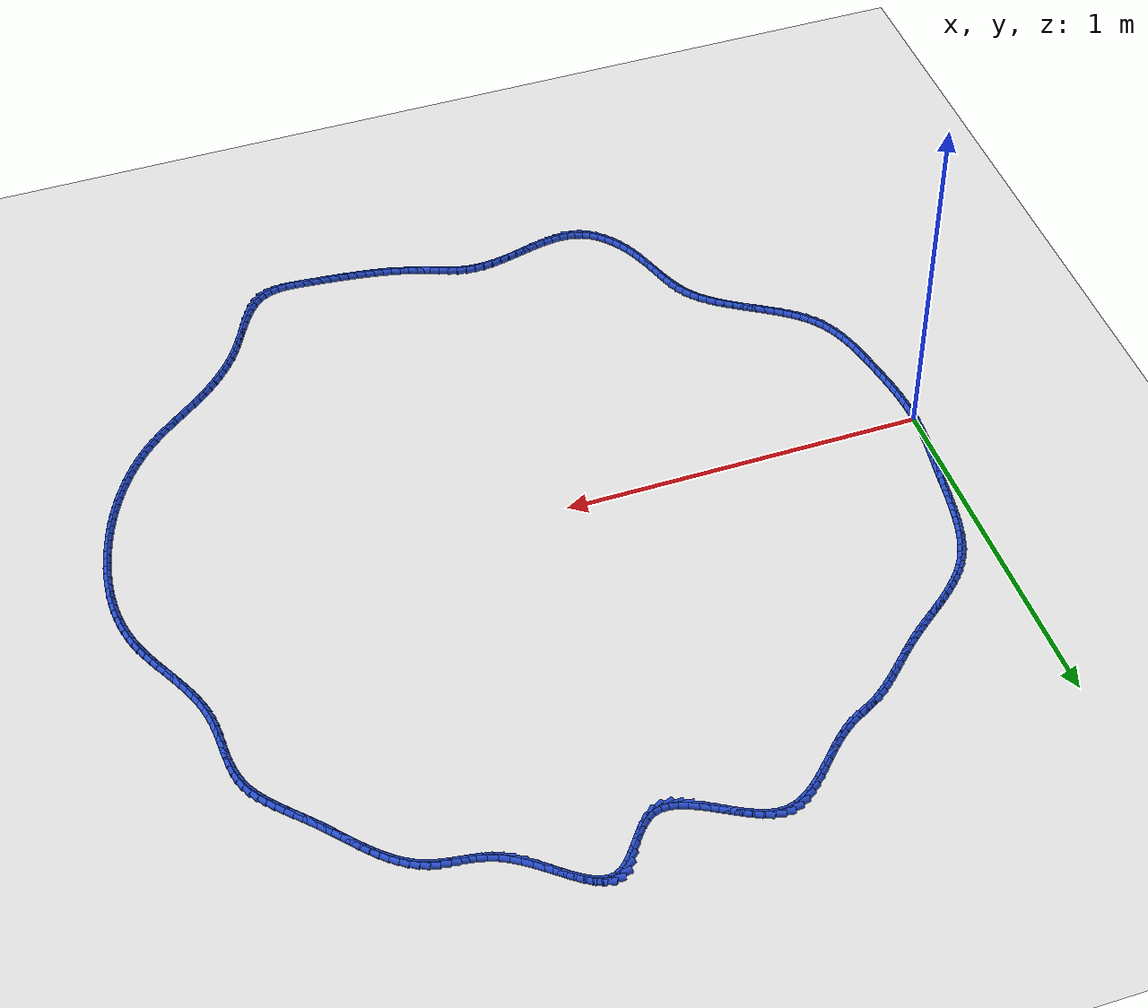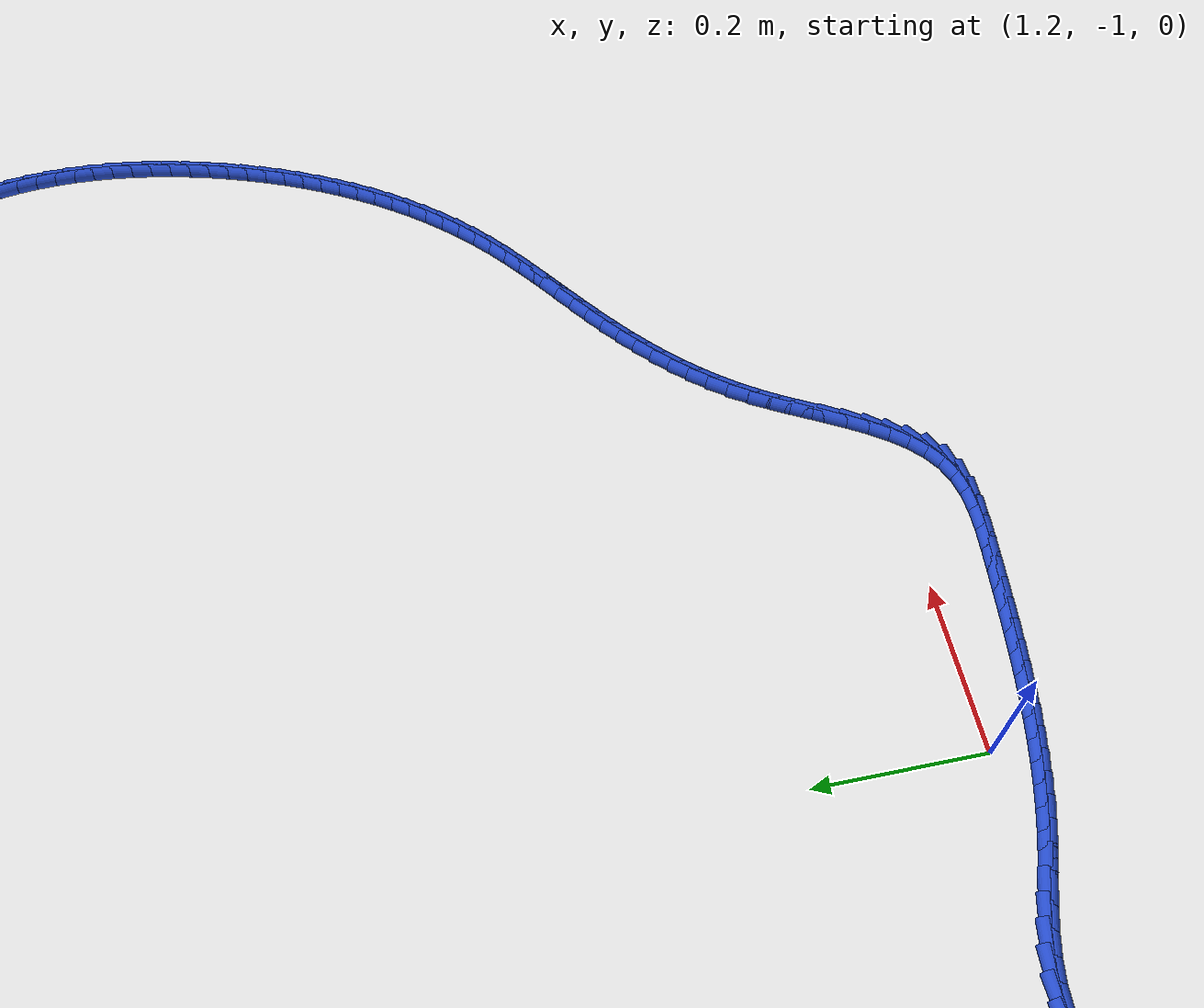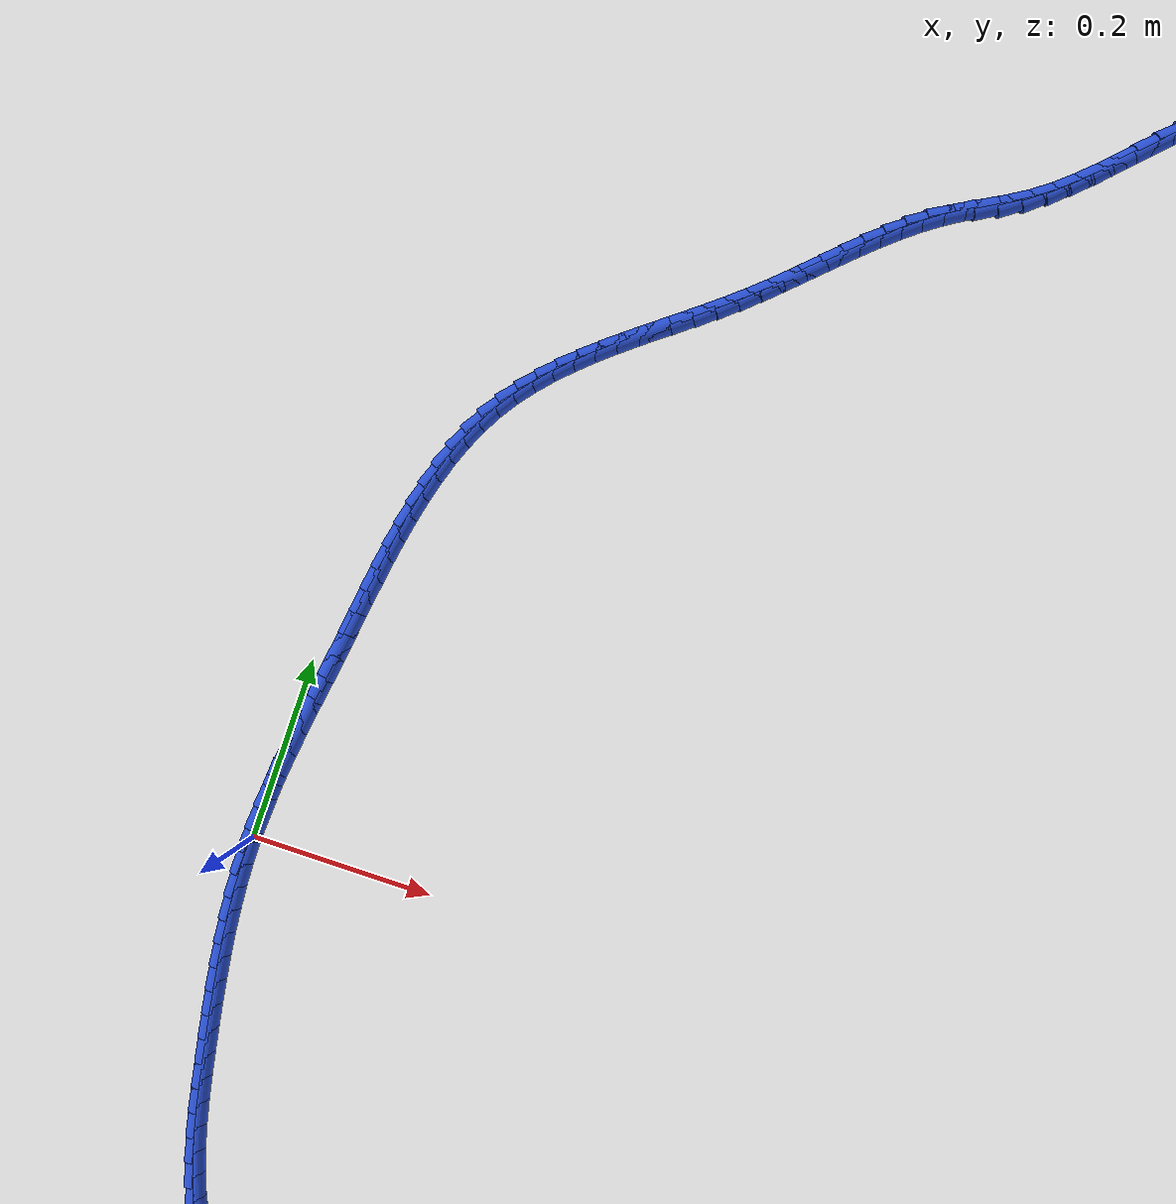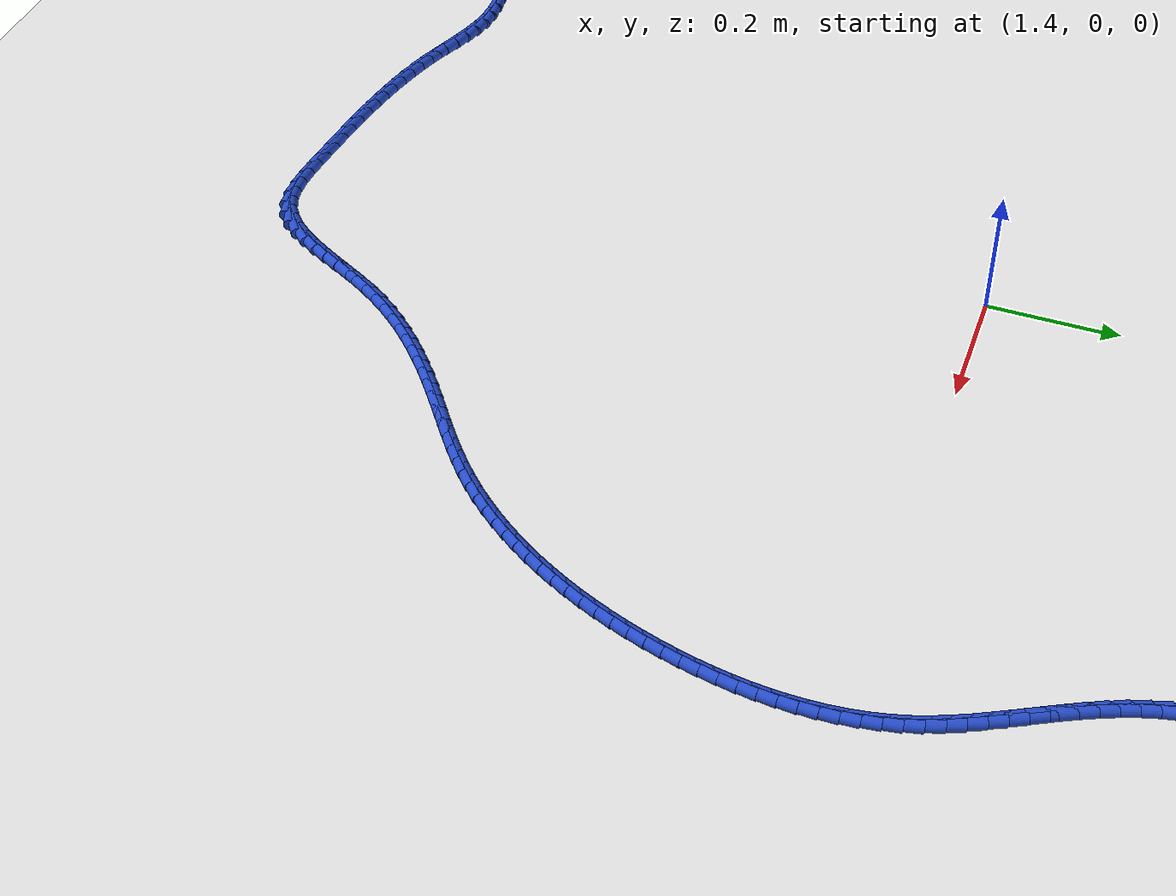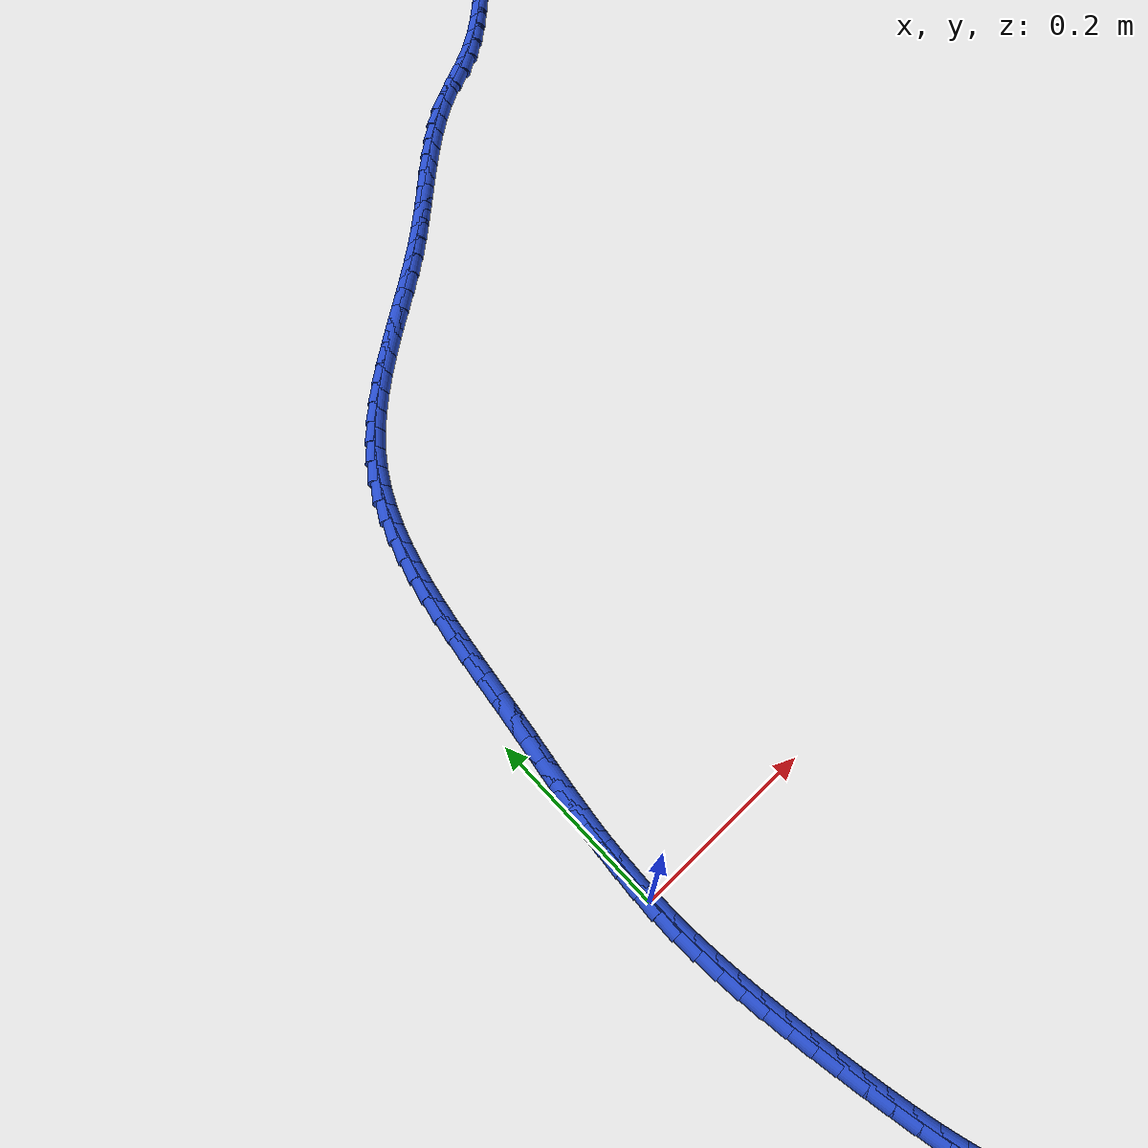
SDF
<sdf version="1.6">
 <world name="default">
  <light name="sun" type="directional">
   <pose>0 0 10 0 -0 0</pose>
   <diffuse>0.8 0.8 0.8 1</diffuse>
   <specular>0.2 0.2 0.2 1</specular>
   <attenuation>
    <range>1000</range>
    <constant>0.9</constant>
    <linear>0.01</linear>
    <quadratic>0.001</quadratic>
   </attenuation>
   <direction>-0.5 0.1 -0.9</direction>
  </light>
  <model name="ground_plane">
   <static>1</static>
   <link name="link">
    <collision name="collision">
     <geometry><plane><normal>0 0 1</normal><size>100 100</size></plane></geometry>
     <surface><friction><ode><mu>100</mu><mu2>50</mu2></ode></friction></surface>
    </collision>
    <visual name="visual">
     <cast_shadows>0</cast_shadows>
     <geometry><plane><normal>0 0 1</normal><size>100 100</size></plane></geometry>
     <material>
      <script><uri>file://media/materials/scripts/gazebo.material</uri><name>Gazebo/WhiteGlow</name></script>
     </material>
    </visual>
   </link>
  </model>
  <gravity>0 0 -9.8</gravity>
  <magnetic_field>6e-06 2.3e-05 -4.2e-05</magnetic_field>
  <atmosphere type="adiabatic"/>
  <physics name="default_physics" default="0" type="ode">
   <max_step_size>0.001</max_step_size>
   <real_time_factor>1</real_time_factor>
   <real_time_update_rate>1000</real_time_update_rate>
  </physics>
  <scene><ambient>0.4 0.4 0.4 1</ambient><background>0.7 0.7 0.7 1</background><shadows>1</shadows></scene>
  <spherical_coordinates>
   <surface_model>EARTH_WGS84</surface_model>
   <latitude_deg>0</latitude_deg>
   <longitude_deg>0</longitude_deg>
   <elevation>0</elevation>
   <heading_deg>0</heading_deg>
  </spherical_coordinates>
  <model name="line">
   <link name="link_0">
    <pose>-5.204170427930421e-18 0.0 0.01 0 1.57 1.5416617803923067</pose>
    <collision name="collision">
     <geometry><cylinder><radius>0.01</radius><length>0.08</length></cylinder></geometry>
    </collision>
    <visual name="visual">
     <material>
      <script><name>Gazebo/Blue</name><uri>file://media/materials/scripts/gazebo.material</uri></script>
     </material>
     <geometry><cylinder><radius>0.01</radius><length>0.08</length></cylinder></geometry>
    </visual>
   </link>
   <link name="link_1">
    <pose>0.0007222507805106315 0.024783169948845978 0.01 0 1.57 1.5083730205306412</pose>
    <collision name="collision">
     <geometry><cylinder><radius>0.01</radius><length>0.08</length></cylinder></geometry>
    </collision>
    <visual name="visual">
     <material>
      <script><name>Gazebo/Blue</name><uri>file://media/materials/scripts/gazebo.material</uri></script>
     </material>
     <geometry><cylinder><radius>0.01</radius><length>0.08</length></cylinder></geometry>
    </visual>
   </link>
   <link name="link_2">
    <pose>0.0022718591314617705 0.04957511305696374 0.01 0 1.57 1.4804635396925818</pose>
    <collision name="collision">
     <geometry><cylinder><radius>0.01</radius><length>0.08</length></cylinder></geometry>
    </collision>
    <visual name="visual">
     <material>
      <script><name>Gazebo/Blue</name><uri>file://media/materials/scripts/gazebo.material</uri></script>
     </material>
     <geometry><cylinder><radius>0.01</radius><length>0.08</length></cylinder></geometry>
    </visual>
   </link>
   <link name="link_3">
    <pose>0.004520885112510516 0.07440447305542623 0.01 0 1.57 1.4579832823140808</pose>
    <collision name="collision">
     <geometry><cylinder><radius>0.01</radius><length>0.08</length></cylinder></geometry>
    </collision>
    <visual name="visual">
     <material>
      <script><name>Gazebo/Blue</name><uri>file://media/materials/scripts/gazebo.material</uri></script>
     </material>
     <geometry><cylinder><radius>0.01</radius><length>0.08</length></cylinder></geometry>
    </visual>
   </link>
   <link name="link_4">
    <pose>0.007341388783313968 0.09929989367530627 0.01 0 1.57 1.440918312579927</pose>
    <collision name="collision">
     <geometry><cylinder><radius>0.01</radius><length>0.08</length></cylinder></geometry>
    </collision>
    <visual name="visual">
     <material>
      <script><name>Gazebo/Blue</name><uri>file://media/materials/scripts/gazebo.material</uri></script>
     </material>
     <geometry><cylinder><radius>0.01</radius><length>0.08</length></cylinder></geometry>
    </visual>
   </link>
   <link name="link_5">
    <pose>0.01060543020352924 0.12429001864767683 0.01 0 1.57 1.4292114604930566</pose>
    <collision name="collision">
     <geometry><cylinder><radius>0.01</radius><length>0.08</length></cylinder></geometry>
    </collision>
    <visual name="visual">
     <material>
      <script><name>Gazebo/Blue</name><uri>file://media/materials/scripts/gazebo.material</uri></script>
     </material>
     <geometry><cylinder><radius>0.01</radius><length>0.08</length></cylinder></geometry>
    </visual>
   </link>
   <link name="link_6">
    <pose>0.014185069432813422 0.14940349170361078 0.01 0 1.57 1.4227783164318215</pose>
    <collision name="collision">
     <geometry><cylinder><radius>0.01</radius><length>0.08</length></cylinder></geometry>
    </collision>
    <visual name="visual">
     <material>
      <script><name>Gazebo/Blue</name><uri>file://media/materials/scripts/gazebo.material</uri></script>
     </material>
     <geometry><cylinder><radius>0.01</radius><length>0.08</length></cylinder></geometry>
    </visual>
   </link>
   <link name="link_7">
    <pose>0.017952366530823632 0.17466895657418105 0.01 0 1.57 1.4215182199162297</pose>
    <collision name="collision">
     <geometry><cylinder><radius>0.01</radius><length>0.08</length></cylinder></geometry>
    </collision>
    <visual name="visual">
     <material>
      <script><name>Gazebo/Blue</name><uri>file://media/materials/scripts/gazebo.material</uri></script>
     </material>
     <geometry><cylinder><radius>0.01</radius><length>0.08</length></cylinder></geometry>
    </visual>
   </link>
   <link name="link_8">
    <pose>0.021779381557216967 0.20011505699046056 0.01 0 1.57 1.4253166032420594</pose>
    <collision name="collision">
     <geometry><cylinder><radius>0.01</radius><length>0.08</length></cylinder></geometry>
    </collision>
    <visual name="visual">
     <material>
      <script><name>Gazebo/Blue</name><uri>file://media/materials/scripts/gazebo.material</uri></script>
     </material>
     <geometry><cylinder><radius>0.01</radius><length>0.08</length></cylinder></geometry>
    </visual>
   </link>
   <link name="link_9">
    <pose>0.025538268037186118 0.2257703907212635 0.01 0 1.57 1.4313777457403511</pose>
    <collision name="collision">
     <geometry><cylinder><radius>0.01</radius><length>0.08</length></cylinder></geometry>
    </collision>
    <visual name="visual">
     <material>
      <script><name>Gazebo/Blue</name><uri>file://media/materials/scripts/gazebo.material</uri></script>
     </material>
     <geometry><cylinder><radius>0.01</radius><length>0.08</length></cylinder></geometry>
    </visual>
   </link>
   <link name="link_10">
    <pose>0.02916726873446623 0.2516310557411657 0.01 0 1.57 1.4323362552272612</pose>
    <collision name="collision">
     <geometry><cylinder><radius>0.01</radius><length>0.08</length></cylinder></geometry>
    </collision>
    <visual name="visual">
     <material>
      <script><name>Gazebo/Blue</name><uri>file://media/materials/scripts/gazebo.material</uri></script>
     </material>
     <geometry><cylinder><radius>0.01</radius><length>0.08</length></cylinder></geometry>
    </visual>
   </link>
   <link name="link_11">
    <pose>0.03278659663364936 0.27760366503647804 0.01 0 1.57 1.427010615349144</pose>
    <collision name="collision">
     <geometry><cylinder><radius>0.01</radius><length>0.08</length></cylinder></geometry>
    </collision>
    <visual name="visual">
     <material>
      <script><name>Gazebo/Blue</name><uri>file://media/materials/scripts/gazebo.material</uri></script>
     </material>
     <geometry><cylinder><radius>0.01</radius><length>0.08</length></cylinder></geometry>
    </visual>
   </link>
   <link name="link_12">
    <pose>0.03654751356184786 0.30357956313202666 0.01 0 1.57 1.4153657907886936</pose>
    <collision name="collision">
     <geometry><cylinder><radius>0.01</radius><length>0.08</length></cylinder></geometry>
    </collision>
    <visual name="visual">
     <material>
      <script><name>Gazebo/Blue</name><uri>file://media/materials/scripts/gazebo.material</uri></script>
     </material>
     <geometry><cylinder><radius>0.01</radius><length>0.08</length></cylinder></geometry>
    </visual>
   </link>
   <link name="link_13">
    <pose>0.040601281346174065 0.3294500945526377 0.01 0 1.57 1.3972484574126967</pose>
    <collision name="collision">
     <geometry><cylinder><radius>0.01</radius><length>0.08</length></cylinder></geometry>
    </collision>
    <visual name="visual">
     <material>
      <script><name>Gazebo/Blue</name><uri>file://media/materials/scripts/gazebo.material</uri></script>
     </material>
     <geometry><cylinder><radius>0.01</radius><length>0.08</length></cylinder></geometry>
    </visual>
   </link>
   <link name="link_14">
    <pose>0.04509916181374028 0.35510660382313697 0.01 0 1.57 1.3723956001713247</pose>
    <collision name="collision">
     <geometry><cylinder><radius>0.01</radius><length>0.08</length></cylinder></geometry>
    </collision>
    <visual name="visual">
     <material>
      <script><name>Gazebo/Blue</name><uri>file://media/materials/scripts/gazebo.material</uri></script>
     </material>
     <geometry><cylinder><radius>0.01</radius><length>0.08</length></cylinder></geometry>
    </visual>
   </link>
   <link name="link_15">
    <pose>0.050192416791658895 0.3804404354683509 0.01 0 1.57 1.3404485300727265</pose>
    <collision name="collision">
     <geometry><cylinder><radius>0.01</radius><length>0.08</length></cylinder></geometry>
    </collision>
    <visual name="visual">
     <material>
      <script><name>Gazebo/Blue</name><uri>file://media/materials/scripts/gazebo.material</uri></script>
     </material>
     <geometry><cylinder><radius>0.01</radius><length>0.08</length></cylinder></geometry>
    </visual>
   </link>
   <link name="link_16">
    <pose>0.056032308107042204 0.4053429340131051 0.01 0 1.57 1.3009768018593943</pose>
    <collision name="collision">
     <geometry><cylinder><radius>0.01</radius><length>0.08</length></cylinder></geometry>
    </collision>
    <visual name="visual">
     <material>
      <script><name>Gazebo/Blue</name><uri>file://media/materials/scripts/gazebo.material</uri></script>
     </material>
     <geometry><cylinder><radius>0.01</radius><length>0.08</length></cylinder></geometry>
    </visual>
   </link>
   <link name="link_17">
    <pose>0.06277009758700258 0.4297054439822261 0.01 0 1.57 1.2535183638982366</pose>
    <collision name="collision">
     <geometry><cylinder><radius>0.01</radius><length>0.08</length></cylinder></geometry>
    </collision>
    <visual name="visual">
     <material>
      <script><name>Gazebo/Blue</name><uri>file://media/materials/scripts/gazebo.material</uri></script>
     </material>
     <geometry><cylinder><radius>0.01</radius><length>0.08</length></cylinder></geometry>
    </visual>
   </link>
   <link name="link_18">
    <pose>0.07055704705865233 0.4534193099005396 0.01 0 1.57 1.1976436448500605</pose>
    <collision name="collision">
     <geometry><cylinder><radius>0.01</radius><length>0.08</length></cylinder></geometry>
    </collision>
    <visual name="visual">
     <material>
      <script><name>Gazebo/Blue</name><uri>file://media/materials/scripts/gazebo.material</uri></script>
     </material>
     <geometry><cylinder><radius>0.01</radius><length>0.08</length></cylinder></geometry>
    </visual>
   </link>
   <link name="link_19">
    <pose>0.07954441834910381 0.47637587629287187 0.01 0 1.57 1.133050743131445</pose>
    <collision name="collision">
     <geometry><cylinder><radius>0.01</radius><length>0.08</length></cylinder></geometry>
    </collision>
    <visual name="visual">
     <material>
      <script><name>Gazebo/Blue</name><uri>file://media/materials/scripts/gazebo.material</uri></script>
     </material>
     <geometry><cylinder><radius>0.01</radius><length>0.08</length></cylinder></geometry>
    </visual>
   </link>
   <link name="link_20">
    <pose>0.08988347328546936 0.4984664876840489 0.01 0 1.57 1.0596938997533212</pose>
    <collision name="collision">
     <geometry><cylinder><radius>0.01</radius><length>0.08</length></cylinder></geometry>
    </collision>
    <visual name="visual">
     <material>
      <script><name>Gazebo/Blue</name><uri>file://media/materials/scripts/gazebo.material</uri></script>
     </material>
     <geometry><cylinder><radius>0.01</radius><length>0.08</length></cylinder></geometry>
    </visual>
   </link>
   <link name="link_21">
    <pose>0.10172547369486132 0.5195824885988968 0.01 0 1.57 0.9787237997052846</pose>
    <collision name="collision">
     <geometry><cylinder><radius>0.01</radius><length>0.08</length></cylinder></geometry>
    </collision>
    <visual name="visual">
     <material>
      <script><name>Gazebo/Blue</name><uri>file://media/materials/scripts/gazebo.material</uri></script>
     </material>
     <geometry><cylinder><radius>0.01</radius><length>0.08</length></cylinder></geometry>
    </visual>
   </link>
   <link name="link_22">
    <pose>0.11520621504434371 0.5396263684701199 0.01 0 1.57 0.9009672411544195</pose>
    <collision name="collision">
     <geometry><cylinder><radius>0.01</radius><length>0.08</length></cylinder></geometry>
    </collision>
    <visual name="visual">
     <material>
      <script><name>Gazebo/Blue</name><uri>file://media/materials/scripts/gazebo.material</uri></script>
     </material>
     <geometry><cylinder><radius>0.01</radius><length>0.08</length></cylinder></geometry>
    </visual>
   </link>
   <link name="link_23">
    <pose>0.13026582994640412 0.5586416094709648 0.01 0 1.57 0.8340236462627421</pose>
    <collision name="collision">
     <geometry><cylinder><radius>0.01</radius><length>0.08</length></cylinder></geometry>
    </collision>
    <visual name="visual">
     <material>
      <script><name>Gazebo/Blue</name><uri>file://media/materials/scripts/gazebo.material</uri></script>
     </material>
     <geometry><cylinder><radius>0.01</radius><length>0.08</length></cylinder></geometry>
    </visual>
   </link>
   <link name="link_24">
    <pose>0.1467102501913302 0.5767683975754384 0.01 0 1.57 0.7781974574996203</pose>
    <collision name="collision">
     <geometry><cylinder><radius>0.01</radius><length>0.08</length></cylinder></geometry>
    </collision>
    <visual name="visual">
     <material>
      <script><name>Gazebo/Blue</name><uri>file://media/materials/scripts/gazebo.material</uri></script>
     </material>
     <geometry><cylinder><radius>0.01</radius><length>0.08</length></cylinder></geometry>
    </visual>
   </link>
   <link name="link_25">
    <pose>0.16434278410048048 0.5941488092036153 0.01 0 1.57 0.7332466025543669</pose>
    <collision name="collision">
     <geometry><cylinder><radius>0.01</radius><length>0.08</length></cylinder></geometry>
    </collision>
    <visual name="visual">
     <material>
      <script><name>Gazebo/Blue</name><uri>file://media/materials/scripts/gazebo.material</uri></script>
     </material>
     <geometry><cylinder><radius>0.01</radius><length>0.08</length></cylinder></geometry>
    </visual>
   </link>
   <link name="link_26">
    <pose>0.18296673999521357 0.6109249207755699 0.01 0 1.57 0.6987259892979459</pose>
    <collision name="collision">
     <geometry><cylinder><radius>0.01</radius><length>0.08</length></cylinder></geometry>
    </collision>
    <visual name="visual">
     <material>
      <script><name>Gazebo/Blue</name><uri>file://media/materials/scripts/gazebo.material</uri></script>
     </material>
     <geometry><cylinder><radius>0.01</radius><length>0.08</length></cylinder></geometry>
    </visual>
   </link>
   <link name="link_27">
    <pose>0.2023854261968882 0.6272388087113765 0.01 0 1.57 0.6741424017186908</pose>
    <collision name="collision">
     <geometry><cylinder><radius>0.01</radius><length>0.08</length></cylinder></geometry>
    </collision>
    <visual name="visual">
     <material>
      <script><name>Gazebo/Blue</name><uri>file://media/materials/scripts/gazebo.material</uri></script>
     </material>
     <geometry><cylinder><radius>0.01</radius><length>0.08</length></cylinder></geometry>
    </visual>
   </link>
   <link name="link_28">
    <pose>0.22240215102686312 0.6432325494311097 0.01 0 1.57 0.6590549604459279</pose>
    <collision name="collision">
     <geometry><cylinder><radius>0.01</radius><length>0.08</length></cylinder></geometry>
    </collision>
    <visual name="visual">
     <material>
      <script><name>Gazebo/Blue</name><uri>file://media/materials/scripts/gazebo.material</uri></script>
     </material>
     <geometry><cylinder><radius>0.01</radius><length>0.08</length></cylinder></geometry>
    </visual>
   </link>
   <link name="link_29">
    <pose>0.24282022280649682 0.6590482193548438 0.01 0 1.57 0.6531328040601314</pose>
    <collision name="collision">
     <geometry><cylinder><radius>0.01</radius><length>0.08</length></cylinder></geometry>
    </collision>
    <visual name="visual">
     <material>
      <script><name>Gazebo/Blue</name><uri>file://media/materials/scripts/gazebo.material</uri></script>
     </material>
     <geometry><cylinder><radius>0.01</radius><length>0.08</length></cylinder></geometry>
    </visual>
   </link>
   <link name="link_30">
    <pose>0.26344294985714806 0.6748278949026532 0.01 0 1.57 0.6561825459402939</pose>
    <collision name="collision">
     <geometry><cylinder><radius>0.01</radius><length>0.08</length></cylinder></geometry>
    </collision>
    <visual name="visual">
     <material>
      <script><name>Gazebo/Blue</name><uri>file://media/materials/scripts/gazebo.material</uri></script>
     </material>
     <geometry><cylinder><radius>0.01</radius><length>0.08</length></cylinder></geometry>
    </visual>
   </link>
   <link name="link_31">
    <pose>0.2840736405001753 0.6907136524946123 0.01 0 1.57 0.6681545322979969</pose>
    <collision name="collision">
     <geometry><cylinder><radius>0.01</radius><length>0.08</length></cylinder></geometry>
    </collision>
    <visual name="visual">
     <material>
      <script><name>Gazebo/Blue</name><uri>file://media/materials/scripts/gazebo.material</uri></script>
     </material>
     <geometry><cylinder><radius>0.01</radius><length>0.08</length></cylinder></geometry>
    </visual>
   </link>
   <link name="link_32">
    <pose>0.30451560305693753 0.7068475685507958 0.01 0 1.57 0.6891322635207688</pose>
    <collision name="collision">
     <geometry><cylinder><radius>0.01</radius><length>0.08</length></cylinder></geometry>
    </collision>
    <visual name="visual">
     <material>
      <script><name>Gazebo/Blue</name><uri>file://media/materials/scripts/gazebo.material</uri></script>
     </material>
     <geometry><cylinder><radius>0.01</radius><length>0.08</length></cylinder></geometry>
    </visual>
   </link>
   <link name="link_33">
    <pose>0.3245721458487931 0.7233717194912779 0.01 0 1.57 0.7177177502858603</pose>
    <collision name="collision">
     <geometry><cylinder><radius>0.01</radius><length>0.08</length></cylinder></geometry>
    </collision>
    <visual name="visual">
     <material>
      <script><name>Gazebo/Blue</name><uri>file://media/materials/scripts/gazebo.material</uri></script>
     </material>
     <geometry><cylinder><radius>0.01</radius><length>0.08</length></cylinder></geometry>
    </visual>
   </link>
   <link name="link_34">
    <pose>0.34407607652165456 0.7403993939381728 0.01 0 1.57 0.7418191239127402</pose>
    <collision name="collision">
     <geometry><cylinder><radius>0.01</radius><length>0.08</length></cylinder></geometry>
    </collision>
    <visual name="visual">
     <material>
      <script><name>Gazebo/Blue</name><uri>file://media/materials/scripts/gazebo.material</uri></script>
     </material>
     <geometry><cylinder><radius>0.01</radius><length>0.08</length></cylinder></geometry>
    </visual>
   </link>
   <link name="link_35">
    <pose>0.36308750861493017 0.7578220572604825 0.01 0 1.57 0.7556846395429466</pose>
    <collision name="collision">
     <geometry><cylinder><radius>0.01</radius><length>0.08</length></cylinder></geometry>
    </collision>
    <visual name="visual">
     <material>
      <script><name>Gazebo/Blue</name><uri>file://media/materials/scripts/gazebo.material</uri></script>
     </material>
     <geometry><cylinder><radius>0.01</radius><length>0.08</length></cylinder></geometry>
    </visual>
   </link>
   <link name="link_36">
    <pose>0.3817721860374812 0.7754280922725988 0.01 0 1.57 0.7591716916741622</pose>
    <collision name="collision">
     <geometry><cylinder><radius>0.01</radius><length>0.08</length></cylinder></geometry>
    </collision>
    <visual name="visual">
     <material>
      <script><name>Gazebo/Blue</name><uri>file://media/materials/scripts/gazebo.material</uri></script>
     </material>
     <geometry><cylinder><radius>0.01</radius><length>0.08</length></cylinder></geometry>
    </visual>
   </link>
   <link name="link_37">
    <pose>0.400296436835997 0.7930053117405467 0.01 0 1.57 0.7521220093707346</pose>
    <collision name="collision">
     <geometry><cylinder><radius>0.01</radius><length>0.08</length></cylinder></geometry>
    </collision>
    <visual name="visual">
     <material>
      <script><name>Gazebo/Blue</name><uri>file://media/materials/scripts/gazebo.material</uri></script>
     </material>
     <geometry><cylinder><radius>0.01</radius><length>0.08</length></cylinder></geometry>
    </visual>
   </link>
   <link name="link_38">
    <pose>0.418826589057167 0.810341528430351 0.01 0 1.57 0.7343162068795231</pose>
    <collision name="collision">
     <geometry><cylinder><radius>0.01</radius><length>0.08</length></cylinder></geometry>
    </collision>
    <visual name="visual">
     <material>
      <script><name>Gazebo/Blue</name><uri>file://media/materials/scripts/gazebo.material</uri></script>
     </material>
     <geometry><cylinder><radius>0.01</radius><length>0.08</length></cylinder></geometry>
    </visual>
   </link>
   <link name="link_39">
    <pose>0.4375289707476808 0.8272245551080375 0.01 0 1.57 0.7054948305214743</pose>
    <collision name="collision">
     <geometry><cylinder><radius>0.01</radius><length>0.08</length></cylinder></geometry>
    </collision>
    <visual name="visual">
     <material>
      <script><name>Gazebo/Blue</name><uri>file://media/materials/scripts/gazebo.material</uri></script>
     </material>
     <geometry><cylinder><radius>0.01</radius><length>0.08</length></cylinder></geometry>
    </visual>
   </link>
   <link name="link_40">
    <pose>0.4565699099542275 0.8434422045396306 0.01 0 1.57 0.6654202031688906</pose>
    <collision name="collision">
     <geometry><cylinder><radius>0.01</radius><length>0.08</length></cylinder></geometry>
    </collision>
    <visual name="visual">
     <material>
      <script><name>Gazebo/Blue</name><uri>file://media/materials/scripts/gazebo.material</uri></script>
     </material>
     <geometry><cylinder><radius>0.01</radius><length>0.08</length></cylinder></geometry>
    </visual>
   </link>
   <link name="link_41">
    <pose>0.47611573472349683 0.8587822894911561 0.01 0 1.57 0.6139852760800283</pose>
    <collision name="collision">
     <geometry><cylinder><radius>0.01</radius><length>0.08</length></cylinder></geometry>
    </collision>
    <visual name="visual">
     <material>
      <script><name>Gazebo/Blue</name><uri>file://media/materials/scripts/gazebo.material</uri></script>
     </material>
     <geometry><cylinder><radius>0.01</radius><length>0.08</length></cylinder></geometry>
    </visual>
   </link>
   <link name="link_42">
    <pose>0.49633277310217794 0.8730326227286385 0.01 0 1.57 0.5516562379806169</pose>
    <collision name="collision">
     <geometry><cylinder><radius>0.01</radius><length>0.08</length></cylinder></geometry>
    </collision>
    <visual name="visual">
     <material>
      <script><name>Gazebo/Blue</name><uri>file://media/materials/scripts/gazebo.material</uri></script>
     </material>
     <geometry><cylinder><radius>0.01</radius><length>0.08</length></cylinder></geometry>
    </visual>
   </link>
   <link name="link_43">
    <pose>0.5173843189058933 0.885987456584238 0.01 0 1.57 0.5002331212302688</pose>
    <collision name="collision">
     <geometry><cylinder><radius>0.01</radius><length>0.08</length></cylinder></geometry>
    </collision>
    <visual name="visual">
     <material>
      <script><name>Gazebo/Blue</name><uri>file://media/materials/scripts/gazebo.material</uri></script>
     </material>
     <geometry><cylinder><radius>0.01</radius><length>0.08</length></cylinder></geometry>
    </visual>
   </link>
   <link name="link_44">
    <pose>0.5392093416961226 0.8979171280515535 0.01 0 1.57 0.49518784064513244</pose>
    <collision name="collision">
     <geometry><cylinder><radius>0.01</radius><length>0.08</length></cylinder></geometry>
    </collision>
    <visual name="visual">
     <material>
      <script><name>Gazebo/Blue</name><uri>file://media/materials/scripts/gazebo.material</uri></script>
     </material>
     <geometry><cylinder><radius>0.01</radius><length>0.08</length></cylinder></geometry>
    </visual>
   </link>
   <link name="link_45">
    <pose>0.5613723425060816 0.9098867108466042 0.01 0 1.57 0.5381493836028252</pose>
    <collision name="collision">
     <geometry><cylinder><radius>0.01</radius><length>0.08</length></cylinder></geometry>
    </collision>
    <visual name="visual">
     <material>
      <script><name>Gazebo/Blue</name><uri>file://media/materials/scripts/gazebo.material</uri></script>
     </material>
     <geometry><cylinder><radius>0.01</radius><length>0.08</length></cylinder></geometry>
    </visual>
   </link>
   <link name="link_46">
    <pose>0.5834022649362762 0.9230367424304179 0.01 0 1.57 0.6196967519977901</pose>
    <collision name="collision">
     <geometry><cylinder><radius>0.01</radius><length>0.08</length></cylinder></geometry>
    </collision>
    <visual name="visual">
     <material>
      <script><name>Gazebo/Blue</name><uri>file://media/materials/scripts/gazebo.material</uri></script>
     </material>
     <geometry><cylinder><radius>0.01</radius><length>0.08</length></cylinder></geometry>
    </visual>
   </link>
   <link name="link_47">
    <pose>0.6048788949885537 0.9383592721148393 0.01 0 1.57 0.6945026428307578</pose>
    <collision name="collision">
     <geometry><cylinder><radius>0.01</radius><length>0.08</length></cylinder></geometry>
    </collision>
    <visual name="visual">
     <material>
      <script><name>Gazebo/Blue</name><uri>file://media/materials/scripts/gazebo.material</uri></script>
     </material>
     <geometry><cylinder><radius>0.01</radius><length>0.08</length></cylinder></geometry>
    </visual>
   </link>
   <link name="link_48">
    <pose>0.6257574891639958 0.9557497660836072 0.01 0 1.57 0.746168052050334</pose>
    <collision name="collision">
     <geometry><cylinder><radius>0.01</radius><length>0.08</length></cylinder></geometry>
    </collision>
    <visual name="visual">
     <material>
      <script><name>Gazebo/Blue</name><uri>file://media/materials/scripts/gazebo.material</uri></script>
     </material>
     <geometry><cylinder><radius>0.01</radius><length>0.08</length></cylinder></geometry>
    </visual>
   </link>
   <link name="link_49">
    <pose>0.6461614788615929 0.9746125260854487 0.01 0 1.57 0.7774419466717903</pose>
    <collision name="collision">
     <geometry><cylinder><radius>0.01</radius><length>0.08</length></cylinder></geometry>
    </collision>
    <visual name="visual">
     <material>
      <script><name>Gazebo/Blue</name><uri>file://media/materials/scripts/gazebo.material</uri></script>
     </material>
     <geometry><cylinder><radius>0.01</radius><length>0.08</length></cylinder></geometry>
    </visual>
   </link>
   <link name="link_50">
    <pose>0.6662150863589686 0.9943495440626857 0.01 0 1.57 0.7900622104804292</pose>
    <collision name="collision">
     <geometry><cylinder><radius>0.01</radius><length>0.08</length></cylinder></geometry>
    </collision>
    <visual name="visual">
     <material>
      <script><name>Gazebo/Blue</name><uri>file://media/materials/scripts/gazebo.material</uri></script>
     </material>
     <geometry><cylinder><radius>0.01</radius><length>0.08</length></cylinder></geometry>
    </visual>
   </link>
   <link name="link_51">
    <pose>0.6860425339337464 1.0143628119576398 0.01 0 1.57 0.7845355876205543</pose>
    <collision name="collision">
     <geometry><cylinder><radius>0.01</radius><length>0.08</length></cylinder></geometry>
    </collision>
    <visual name="visual">
     <material>
      <script><name>Gazebo/Blue</name><uri>file://media/materials/scripts/gazebo.material</uri></script>
     </material>
     <geometry><cylinder><radius>0.01</radius><length>0.08</length></cylinder></geometry>
    </visual>
   </link>
   <link name="link_52">
    <pose>0.7057680438635491 1.0340543217126326 0.01 0 1.57 0.7600644695050053</pose>
    <collision name="collision">
     <geometry><cylinder><radius>0.01</radius><length>0.08</length></cylinder></geometry>
    </collision>
    <visual name="visual">
     <material>
      <script><name>Gazebo/Blue</name><uri>file://media/materials/scripts/gazebo.material</uri></script>
     </material>
     <geometry><cylinder><radius>0.01</radius><length>0.08</length></cylinder></geometry>
    </visual>
   </link>
   <link name="link_53">
    <pose>0.7255158384260005 1.0528260652699852 0.01 0 1.57 0.7144419798707244</pose>
    <collision name="collision">
     <geometry><cylinder><radius>0.01</radius><length>0.08</length></cylinder></geometry>
    </collision>
    <visual name="visual">
     <material>
      <script><name>Gazebo/Blue</name><uri>file://media/materials/scripts/gazebo.material</uri></script>
     </material>
     <geometry><cylinder><radius>0.01</radius><length>0.08</length></cylinder></geometry>
    </visual>
   </link>
   <link name="link_54">
    <pose>0.7454101398987238 1.07008003457202 0.01 0 1.57 0.6439584247954059</pose>
    <collision name="collision">
     <geometry><cylinder><radius>0.01</radius><length>0.08</length></cylinder></geometry>
    </collision>
    <visual name="visual">
     <material>
      <script><name>Gazebo/Blue</name><uri>file://media/materials/scripts/gazebo.material</uri></script>
     </material>
     <geometry><cylinder><radius>0.01</radius><length>0.08</length></cylinder></geometry>
    </visual>
   </link>
   <link name="link_55">
    <pose>0.7655751705593425 1.0852182215610582 0.01 0 1.57 0.543575247123414</pose>
    <collision name="collision">
     <geometry><cylinder><radius>0.01</radius><length>0.08</length></cylinder></geometry>
    </collision>
    <visual name="visual">
     <material>
      <script><name>Gazebo/Blue</name><uri>file://media/materials/scripts/gazebo.material</uri></script>
     </material>
     <geometry><cylinder><radius>0.01</radius><length>0.08</length></cylinder></geometry>
    </visual>
   </link>
   <link name="link_56">
    <pose>0.7861351526854798 1.0976426181794208 0.01 0 1.57 0.4080406911066305</pose>
    <collision name="collision">
     <geometry><cylinder><radius>0.01</radius><length>0.08</length></cylinder></geometry>
    </collision>
    <visual name="visual">
     <material>
      <script><name>Gazebo/Blue</name><uri>file://media/materials/scripts/gazebo.material</uri></script>
     </material>
     <geometry><cylinder><radius>0.01</radius><length>0.08</length></cylinder></geometry>
    </visual>
   </link>
   <link name="link_57">
    <pose>0.8072143085547592 1.1067552163694303 0.01 0 1.57 0.2350826305279424</pose>
    <collision name="collision">
     <geometry><cylinder><radius>0.01</radius><length>0.08</length></cylinder></geometry>
    </collision>
    <visual name="visual">
     <material>
      <script><name>Gazebo/Blue</name><uri>file://media/materials/scripts/gazebo.material</uri></script>
     </material>
     <geometry><cylinder><radius>0.01</radius><length>0.08</length></cylinder></geometry>
    </visual>
   </link>
   <link name="link_58">
    <pose>0.8289368604448034 1.1119580080734075 0.01 0 1.57 0.030891543774336182</pose>
    <collision name="collision">
     <geometry><cylinder><radius>0.01</radius><length>0.08</length></cylinder></geometry>
    </collision>
    <visual name="visual">
     <material>
      <script><name>Gazebo/Blue</name><uri>file://media/materials/scripts/gazebo.material</uri></script>
     </material>
     <geometry><cylinder><radius>0.01</radius><length>0.08</length></cylinder></geometry>
    </visual>
   </link>
   <link name="link_59">
    <pose>0.8514270306332367 1.1126529852336748 0.01 0 1.57 -0.17611103269449285</pose>
    <collision name="collision">
     <geometry><cylinder><radius>0.01</radius><length>0.08</length></cylinder></geometry>
    </collision>
    <visual name="visual">
     <material>
      <script><name>Gazebo/Blue</name><uri>file://media/materials/scripts/gazebo.material</uri></script>
     </material>
     <geometry><cylinder><radius>0.01</radius><length>0.08</length></cylinder></geometry>
    </visual>
   </link>
   <link name="link_60">
    <pose>0.8747592203070425 1.1085009145729026 0.01 0 1.57 -0.3309479313916837</pose>
    <collision name="collision">
     <geometry><cylinder><radius>0.01</radius><length>0.08</length></cylinder></geometry>
    </collision>
    <visual name="visual">
     <material>
      <script><name>Gazebo/Blue</name><uri>file://media/materials/scripts/gazebo.material</uri></script>
     </material>
     <geometry><cylinder><radius>0.01</radius><length>0.08</length></cylinder></geometry>
    </visual>
   </link>
   <link name="link_61">
    <pose>0.8988002419003485 1.100240795611043 0.01 0 1.57 -0.43280350121285166</pose>
    <collision name="collision">
     <geometry><cylinder><radius>0.01</radius><length>0.08</length></cylinder></geometry>
    </collision>
    <visual name="visual">
     <material>
      <script><name>Gazebo/Blue</name><uri>file://media/materials/scripts/gazebo.material</uri></script>
     </material>
     <geometry><cylinder><radius>0.01</radius><length>0.08</length></cylinder></geometry>
    </visual>
   </link>
   <link name="link_62">
    <pose>0.9233628487744431 1.088892415071227 0.01 0 1.57 -0.49427781744935</pose>
    <collision name="collision">
     <geometry><cylinder><radius>0.01</radius><length>0.08</length></cylinder></geometry>
    </collision>
    <visual name="visual">
     <material>
      <script><name>Gazebo/Blue</name><uri>file://media/materials/scripts/gazebo.material</uri></script>
     </material>
     <geometry><cylinder><radius>0.01</radius><length>0.08</length></cylinder></geometry>
    </visual>
   </link>
   <link name="link_63">
    <pose>0.9482597941598242 1.07547556035592 0.01 0 1.57 -0.523789216499806</pose>
    <collision name="collision">
     <geometry><cylinder><radius>0.01</radius><length>0.08</length></cylinder></geometry>
    </collision>
    <visual name="visual">
     <material>
      <script><name>Gazebo/Blue</name><uri>file://media/materials/scripts/gazebo.material</uri></script>
     </material>
     <geometry><cylinder><radius>0.01</radius><length>0.08</length></cylinder></geometry>
    </visual>
   </link>
   <link name="link_64">
    <pose>0.9733038312869892 1.0610100188675897 0.01 0 1.57 -0.5253500131005249</pose>
    <collision name="collision">
     <geometry><cylinder><radius>0.01</radius><length>0.08</length></cylinder></geometry>
    </collision>
    <visual name="visual">
     <material>
      <script><name>Gazebo/Blue</name><uri>file://media/materials/scripts/gazebo.material</uri></script>
     </material>
     <geometry><cylinder><radius>0.01</radius><length>0.08</length></cylinder></geometry>
    </visual>
   </link>
   <link name="link_65">
    <pose>0.9983077133864363 1.0465155780087037 0.01 0 1.57 -0.49900788292303433</pose>
    <collision name="collision">
     <geometry><cylinder><radius>0.01</radius><length>0.08</length></cylinder></geometry>
    </collision>
    <visual name="visual">
     <material>
      <script><name>Gazebo/Blue</name><uri>file://media/materials/scripts/gazebo.material</uri></script>
     </material>
     <geometry><cylinder><radius>0.01</radius><length>0.08</length></cylinder></geometry>
    </visual>
   </link>
   <link name="link_66">
    <pose>1.023084193688663 1.0330120251817274 0.01 0 1.57 -0.44079944357787376</pose>
    <collision name="collision">
     <geometry><cylinder><radius>0.01</radius><length>0.08</length></cylinder></geometry>
    </collision>
    <visual name="visual">
     <material>
      <script><name>Gazebo/Blue</name><uri>file://media/materials/scripts/gazebo.material</uri></script>
     </material>
     <geometry><cylinder><radius>0.01</radius><length>0.08</length></cylinder></geometry>
    </visual>
   </link>
   <link name="link_67">
    <pose>1.047446025424167 1.0215191477891286 0.01 0 1.57 -0.3421548189214092</pose>
    <collision name="collision">
     <geometry><cylinder><radius>0.01</radius><length>0.08</length></cylinder></geometry>
    </collision>
    <visual name="visual">
     <material>
      <script><name>Gazebo/Blue</name><uri>file://media/materials/scripts/gazebo.material</uri></script>
     </material>
     <geometry><cylinder><radius>0.01</radius><length>0.08</length></cylinder></geometry>
    </visual>
   </link>
   <link name="link_68">
    <pose>1.0712059618234464 1.0130567332333742 0.01 0 1.57 -0.18976594186606913</pose>
    <collision name="collision">
     <geometry><cylinder><radius>0.01</radius><length>0.08</length></cylinder></geometry>
    </collision>
    <visual name="visual">
     <material>
      <script><name>Gazebo/Blue</name><uri>file://media/materials/scripts/gazebo.material</uri></script>
     </material>
     <geometry><cylinder><radius>0.01</radius><length>0.08</length></cylinder></geometry>
    </visual>
   </link>
   <link name="link_69">
    <pose>1.0941767561169984 1.008644568916931 0.01 0 1.57 0.029902023998861087</pose>
    <collision name="collision">
     <geometry><cylinder><radius>0.01</radius><length>0.08</length></cylinder></geometry>
    </collision>
    <visual name="visual">
     <material>
      <script><name>Gazebo/Blue</name><uri>file://media/materials/scripts/gazebo.material</uri></script>
     </material>
     <geometry><cylinder><radius>0.01</radius><length>0.08</length></cylinder></geometry>
    </visual>
   </link>
   <link name="link_70">
    <pose>1.1161711615353216 1.0093024422422658 0.01 0 1.57 0.31320119472979313</pose>
    <collision name="collision">
     <geometry><cylinder><radius>0.01</radius><length>0.08</length></cylinder></geometry>
    </collision>
    <visual name="visual">
     <material>
      <script><name>Gazebo/Blue</name><uri>file://media/materials/scripts/gazebo.material</uri></script>
     </material>
     <geometry><cylinder><radius>0.01</radius><length>0.08</length></cylinder></geometry>
    </visual>
   </link>
   <link name="link_71">
    <pose>1.137002148626677 1.0160487825676845 0.01 0 1.57 0.5913728985003605</pose>
    <collision name="collision">
     <geometry><cylinder><radius>0.01</radius><length>0.08</length></cylinder></geometry>
    </collision>
    <visual name="visual">
     <material>
      <script><name>Gazebo/Blue</name><uri>file://media/materials/scripts/gazebo.material</uri></script>
     </material>
     <geometry><cylinder><radius>0.01</radius><length>0.08</length></cylinder></geometry>
    </visual>
   </link>
   <link name="link_72">
    <pose>1.1565941167604836 1.0292056874970004 0.01 0 1.57 0.7714647295257325</pose>
    <collision name="collision">
     <geometry><cylinder><radius>0.01</radius><length>0.08</length></cylinder></geometry>
    </collision>
    <visual name="visual">
     <material>
      <script><name>Gazebo/Blue</name><uri>file://media/materials/scripts/gazebo.material</uri></script>
     </material>
     <geometry><cylinder><radius>0.01</radius><length>0.08</length></cylinder></geometry>
    </visual>
   </link>
   <link name="link_73">
    <pose>1.175164277795667 1.047265435091484 0.01 0 1.57 0.8710166556853384</pose>
    <collision name="collision">
     <geometry><cylinder><radius>0.01</radius><length>0.08</length></cylinder></geometry>
    </collision>
    <visual name="visual">
     <material>
      <script><name>Gazebo/Blue</name><uri>file://media/materials/scripts/gazebo.material</uri></script>
     </material>
     <geometry><cylinder><radius>0.01</radius><length>0.08</length></cylinder></geometry>
    </visual>
   </link>
   <link name="link_74">
    <pose>1.1929773649842972 1.068423336660694 0.01 0 1.57 0.9136900970543028</pose>
    <collision name="collision">
     <geometry><cylinder><radius>0.01</radius><length>0.08</length></cylinder></geometry>
    </collision>
    <visual name="visual">
     <material>
      <script><name>Gazebo/Blue</name><uri>file://media/materials/scripts/gazebo.material</uri></script>
     </material>
     <geometry><cylinder><radius>0.01</radius><length>0.08</length></cylinder></geometry>
    </visual>
   </link>
   <link name="link_75">
    <pose>1.2102981115784477 1.09087470351419 0.01 0 1.57 0.9089419365113233</pose>
    <collision name="collision">
     <geometry><cylinder><radius>0.01</radius><length>0.08</length></cylinder></geometry>
    </collision>
    <visual name="visual">
     <material>
      <script><name>Gazebo/Blue</name><uri>file://media/materials/scripts/gazebo.material</uri></script>
     </material>
     <geometry><cylinder><radius>0.01</radius><length>0.08</length></cylinder></geometry>
    </visual>
   </link>
   <link name="link_76">
    <pose>1.2273912508301894 1.1128148469615307 0.01 0 1.57 0.8531490330658222</pose>
    <collision name="collision">
     <geometry><cylinder><radius>0.01</radius><length>0.08</length></cylinder></geometry>
    </collision>
    <visual name="visual">
     <material>
      <script><name>Gazebo/Blue</name><uri>file://media/materials/scripts/gazebo.material</uri></script>
     </material>
     <geometry><cylinder><radius>0.01</radius><length>0.08</length></cylinder></geometry>
    </visual>
   </link>
   <link name="link_77">
    <pose>1.2445215159915946 1.1324390783122757 0.01 0 1.57 0.7269117447156377</pose>
    <collision name="collision">
     <geometry><cylinder><radius>0.01</radius><length>0.08</length></cylinder></geometry>
    </collision>
    <visual name="visual">
     <material>
      <script><name>Gazebo/Blue</name><uri>file://media/materials/scripts/gazebo.material</uri></script>
     </material>
     <geometry><cylinder><radius>0.01</radius><length>0.08</length></cylinder></geometry>
    </visual>
   </link>
   <link name="link_78">
    <pose>1.261953640314735 1.1479427088759844 0.01 0 1.57 0.489170335091466</pose>
    <collision name="collision">
     <geometry><cylinder><radius>0.01</radius><length>0.08</length></cylinder></geometry>
    </collision>
    <visual name="visual">
     <material>
      <script><name>Gazebo/Blue</name><uri>file://media/materials/scripts/gazebo.material</uri></script>
     </material>
     <geometry><cylinder><radius>0.01</radius><length>0.08</length></cylinder></geometry>
    </visual>
   </link>
   <link name="link_79">
    <pose>1.279952081242337 1.1575236913404596 0.01 0 1.57 0.13872911382044562</pose>
    <collision name="collision">
     <geometry><cylinder><radius>0.01</radius><length>0.08</length></cylinder></geometry>
    </collision>
    <visual name="visual">
     <material>
      <script><name>Gazebo/Blue</name><uri>file://media/materials/scripts/gazebo.material</uri></script>
     </material>
     <geometry><cylinder><radius>0.01</radius><length>0.08</length></cylinder></geometry>
    </visual>
   </link>
   <link name="link_80">
    <pose>1.2987017650354922 1.160141634721758 0.01 0 1.57 -0.1813208368152568</pose>
    <collision name="collision">
     <geometry><cylinder><radius>0.01</radius><length>0.08</length></cylinder></geometry>
    </collision>
    <visual name="visual">
     <material>
      <script><name>Gazebo/Blue</name><uri>file://media/materials/scripts/gazebo.material</uri></script>
     </material>
     <geometry><cylinder><radius>0.01</radius><length>0.08</length></cylinder></geometry>
    </visual>
   </link>
   <link name="link_81">
    <pose>1.3181985091532409 1.156567210223683 0.01 0 1.57 -0.40783194671714057</pose>
    <collision name="collision">
     <geometry><cylinder><radius>0.01</radius><length>0.08</length></cylinder></geometry>
    </collision>
    <visual name="visual">
     <material>
      <script><name>Gazebo/Blue</name><uri>file://media/materials/scripts/gazebo.material</uri></script>
     </material>
     <geometry><cylinder><radius>0.01</radius><length>0.08</length></cylinder></geometry>
    </visual>
   </link>
   <link name="link_82">
    <pose>1.338410632201323 1.1478344407972103 0.01 0 1.57 -0.5515898923646361</pose>
    <collision name="collision">
     <geometry><cylinder><radius>0.01</radius><length>0.08</length></cylinder></geometry>
    </collision>
    <visual name="visual">
     <material>
      <script><name>Gazebo/Blue</name><uri>file://media/materials/scripts/gazebo.material</uri></script>
     </material>
     <geometry><cylinder><radius>0.01</radius><length>0.08</length></cylinder></geometry>
    </visual>
   </link>
   <link name="link_83">
    <pose>1.3593064527854755 1.1349773493933133 0.01 0 1.57 -0.6371300389751188</pose>
    <collision name="collision">
     <geometry><cylinder><radius>0.01</radius><length>0.08</length></cylinder></geometry>
    </collision>
    <visual name="visual">
     <material>
      <script><name>Gazebo/Blue</name><uri>file://media/materials/scripts/gazebo.material</uri></script>
     </material>
     <geometry><cylinder><radius>0.01</radius><length>0.08</length></cylinder></geometry>
    </visual>
   </link>
   <link name="link_84">
    <pose>1.3808542895114364 1.1190299589629673 0.01 0 1.57 -0.6820998795930007</pose>
    <collision name="collision">
     <geometry><cylinder><radius>0.01</radius><length>0.08</length></cylinder></geometry>
    </collision>
    <visual name="visual">
     <material>
      <script><name>Gazebo/Blue</name><uri>file://media/materials/scripts/gazebo.material</uri></script>
     </material>
     <geometry><cylinder><radius>0.01</radius><length>0.08</length></cylinder></geometry>
    </visual>
   </link>
   <link name="link_85">
    <pose>1.4030224609849444 1.1010262924571457 0.01 0 1.57 -0.6963413860198712</pose>
    <collision name="collision">
     <geometry><cylinder><radius>0.01</radius><length>0.08</length></cylinder></geometry>
    </collision>
    <visual name="visual">
     <material>
      <script><name>Gazebo/Blue</name><uri>file://media/materials/scripts/gazebo.material</uri></script>
     </material>
     <geometry><cylinder><radius>0.01</radius><length>0.08</length></cylinder></geometry>
    </visual>
   </link>
   <link name="link_86">
    <pose>1.4257792858117375 1.082000372826823 0.01 0 1.57 -0.6841660044927991</pose>
    <collision name="collision">
     <geometry><cylinder><radius>0.01</radius><length>0.08</length></cylinder></geometry>
    </collision>
    <visual name="visual">
     <material>
      <script><name>Gazebo/Blue</name><uri>file://media/materials/scripts/gazebo.material</uri></script>
     </material>
     <geometry><cylinder><radius>0.01</radius><length>0.08</length></cylinder></geometry>
    </visual>
   </link>
   <link name="link_87">
    <pose>1.449093082597554 1.0629862230229736 0.01 0 1.57 -0.6458872938954713</pose>
    <collision name="collision">
     <geometry><cylinder><radius>0.01</radius><length>0.08</length></cylinder></geometry>
    </collision>
    <visual name="visual">
     <material>
      <script><name>Gazebo/Blue</name><uri>file://media/materials/scripts/gazebo.material</uri></script>
     </material>
     <geometry><cylinder><radius>0.01</radius><length>0.08</length></cylinder></geometry>
    </visual>
   </link>
   <link name="link_88">
    <pose>1.4729321699481317 1.045017865996572 0.01 0 1.57 -0.5784608506104372</pose>
    <collision name="collision">
     <geometry><cylinder><radius>0.01</radius><length>0.08</length></cylinder></geometry>
    </collision>
    <visual name="visual">
     <material>
      <script><name>Gazebo/Blue</name><uri>file://media/materials/scripts/gazebo.material</uri></script>
     </material>
     <geometry><cylinder><radius>0.01</radius><length>0.08</length></cylinder></geometry>
    </visual>
   </link>
   <link name="link_89">
    <pose>1.497264866469209 1.0291293246985926 0.01 0 1.57 -0.4758443204005628</pose>
    <collision name="collision">
     <geometry><cylinder><radius>0.01</radius><length>0.08</length></cylinder></geometry>
    </collision>
    <visual name="visual">
     <material>
      <script><name>Gazebo/Blue</name><uri>file://media/materials/scripts/gazebo.material</uri></script>
     </material>
     <geometry><cylinder><radius>0.01</radius><length>0.08</length></cylinder></geometry>
    </visual>
   </link>
   <link name="link_90">
    <pose>1.5220592031511089 1.0163518062760322 0.01 0 1.57 -0.3506851265806094</pose>
    <collision name="collision">
     <geometry><cylinder><radius>0.01</radius><length>0.08</length></cylinder></geometry>
    </collision>
    <visual name="visual">
     <material>
      <script><name>Gazebo/Blue</name><uri>file://media/materials/scripts/gazebo.material</uri></script>
     </material>
     <geometry><cylinder><radius>0.01</radius><length>0.08</length></cylinder></geometry>
    </visual>
   </link>
   <link name="link_91">
    <pose>1.547224941599173 1.0071460506555572 0.01 0 1.57 -0.24883078111123785</pose>
    <collision name="collision">
     <geometry><cylinder><radius>0.01</radius><length>0.08</length></cylinder></geometry>
    </collision>
    <visual name="visual">
     <material>
      <script><name>Gazebo/Blue</name><uri>file://media/materials/scripts/gazebo.material</uri></script>
     </material>
     <geometry><cylinder><radius>0.01</radius><length>0.08</length></cylinder></geometry>
    </visual>
   </link>
   <link name="link_92">
    <pose>1.5725431407054535 1.0007127762428112 0.01 0 1.57 -0.18140707153791136</pose>
    <collision name="collision">
     <geometry><cylinder><radius>0.01</radius><length>0.08</length></cylinder></geometry>
    </collision>
    <visual name="visual">
     <material>
      <script><name>Gazebo/Blue</name><uri>file://media/materials/scripts/gazebo.material</uri></script>
     </material>
     <geometry><cylinder><radius>0.01</radius><length>0.08</length></cylinder></geometry>
    </visual>
   </link>
   <link name="link_93">
    <pose>1.5977776453584158 0.9960841734114088 0.01 0 1.57 -0.15103026229388786</pose>
    <collision name="collision">
     <geometry><cylinder><radius>0.01</radius><length>0.08</length></cylinder></geometry>
    </collision>
    <visual name="visual">
     <material>
      <script><name>Gazebo/Blue</name><uri>file://media/materials/scripts/gazebo.material</uri></script>
     </material>
     <geometry><cylinder><radius>0.01</radius><length>0.08</length></cylinder></geometry>
    </visual>
   </link>
   <link name="link_94">
    <pose>1.6226923004465241 0.9922924325349637 0.01 0 1.57 -0.15966799688558586</pose>
    <collision name="collision">
     <geometry><cylinder><radius>0.01</radius><length>0.08</length></cylinder></geometry>
    </collision>
    <visual name="visual">
     <material>
      <script><name>Gazebo/Blue</name><uri>file://media/materials/scripts/gazebo.material</uri></script>
     </material>
     <geometry><cylinder><radius>0.01</radius><length>0.08</length></cylinder></geometry>
    </visual>
   </link>
   <link name="link_95">
    <pose>1.6470509508582432 0.9883697439870913 0.01 0 1.57 -0.20993612916218832</pose>
    <collision name="collision">
     <geometry><cylinder><radius>0.01</radius><length>0.08</length></cylinder></geometry>
    </collision>
    <visual name="visual">
     <material>
      <script><name>Gazebo/Blue</name><uri>file://media/materials/scripts/gazebo.material</uri></script>
     </material>
     <geometry><cylinder><radius>0.01</radius><length>0.08</length></cylinder></geometry>
    </visual>
   </link>
   <link name="link_96">
    <pose>1.6706174414820365 0.9833482981414052 0.01 0 1.57 -0.3044229538754298</pose>
    <collision name="collision">
     <geometry><cylinder><radius>0.01</radius><length>0.08</length></cylinder></geometry>
    </collision>
    <visual name="visual">
     <material>
      <script><name>Gazebo/Blue</name><uri>file://media/materials/scripts/gazebo.material</uri></script>
     </material>
     <geometry><cylinder><radius>0.01</radius><length>0.08</length></cylinder></geometry>
    </visual>
   </link>
   <link name="link_97">
    <pose>1.6931574690371498 0.9762664671165922 0.01 0 1.57 -0.4238414345881973</pose>
    <collision name="collision">
     <geometry><cylinder><radius>0.01</radius><length>0.08</length></cylinder></geometry>
    </collision>
    <visual name="visual">
     <material>
      <script><name>Gazebo/Blue</name><uri>file://media/materials/scripts/gazebo.material</uri></script>
     </material>
     <geometry><cylinder><radius>0.01</radius><length>0.08</length></cylinder></geometry>
    </visual>
   </link>
   <link name="link_98">
    <pose>1.7145694427645692 0.9666056413596813 0.01 0 1.57 -0.5326641164342392</pose>
    <collision name="collision">
     <geometry><cylinder><radius>0.01</radius><length>0.08</length></cylinder></geometry>
    </collision>
    <visual name="visual">
     <material>
      <script><name>Gazebo/Blue</name><uri>file://media/materials/scripts/gazebo.material</uri></script>
     </material>
     <geometry><cylinder><radius>0.01</radius><length>0.08</length></cylinder></geometry>
    </visual>
   </link>
   <link name="link_99">
    <pose>1.7349709649168643 0.9545789171153467 0.01 0 1.57 -0.6257067629695859</pose>
    <collision name="collision">
     <geometry><cylinder><radius>0.01</radius><length>0.08</length></cylinder></geometry>
    </collision>
    <visual name="visual">
     <material>
      <script><name>Gazebo/Blue</name><uri>file://media/materials/scripts/gazebo.material</uri></script>
     </material>
     <geometry><cylinder><radius>0.01</radius><length>0.08</length></cylinder></geometry>
    </visual>
   </link>
   <link name="link_100">
    <pose>1.7545001627403085 0.9404679067583172 0.01 0 1.57 -0.702573788124187</pose>
    <collision name="collision">
     <geometry><cylinder><radius>0.01</radius><length>0.08</length></cylinder></geometry>
    </collision>
    <visual name="visual">
     <material>
      <script><name>Gazebo/Blue</name><uri>file://media/materials/scripts/gazebo.material</uri></script>
     </material>
     <geometry><cylinder><radius>0.01</radius><length>0.08</length></cylinder></geometry>
    </visual>
   </link>
   <link name="link_101">
    <pose>1.7732951634811742 0.9245542226633215 0.01 0 1.57 -0.7639558536630183</pose>
    <collision name="collision">
     <geometry><cylinder><radius>0.01</radius><length>0.08</length></cylinder></geometry>
    </collision>
    <visual name="visual">
     <material>
      <script><name>Gazebo/Blue</name><uri>file://media/materials/scripts/gazebo.material</uri></script>
     </material>
     <geometry><cylinder><radius>0.01</radius><length>0.08</length></cylinder></geometry>
    </visual>
   </link>
   <link name="link_102">
    <pose>1.7914940943857336 0.907119477205088 0.01 0 1.57 -0.811019397514967</pose>
    <collision name="collision">
     <geometry><cylinder><radius>0.01</radius><length>0.08</length></cylinder></geometry>
    </collision>
    <visual name="visual">
     <material>
      <script><name>Gazebo/Blue</name><uri>file://media/materials/scripts/gazebo.material</uri></script>
     </material>
     <geometry><cylinder><radius>0.01</radius><length>0.08</length></cylinder></geometry>
    </visual>
   </link>
   <link name="link_103">
    <pose>1.80923508270026 0.8884452827583457 0.01 0 1.57 -0.8449946291841909</pose>
    <collision name="collision">
     <geometry><cylinder><radius>0.01</radius><length>0.08</length></cylinder></geometry>
    </collision>
    <visual name="visual">
     <material>
      <script><name>Gazebo/Blue</name><uri>file://media/materials/scripts/gazebo.material</uri></script>
     </material>
     <geometry><cylinder><radius>0.01</radius><length>0.08</length></cylinder></geometry>
    </visual>
   </link>
   <link name="link_104">
    <pose>1.826656255671026 0.8688132516978224 0.01 0 1.57 -0.8669467407259794</pose>
    <collision name="collision">
     <geometry><cylinder><radius>0.01</radius><length>0.08</length></cylinder></geometry>
    </collision>
    <visual name="visual">
     <material>
      <script><name>Gazebo/Blue</name><uri>file://media/materials/scripts/gazebo.material</uri></script>
     </material>
     <geometry><cylinder><radius>0.01</radius><length>0.08</length></cylinder></geometry>
    </visual>
   </link>
   <link name="link_105">
    <pose>1.8438957405443044 0.8485049963982481 0.01 0 1.57 -0.8776698323023392</pose>
    <collision name="collision">
     <geometry><cylinder><radius>0.01</radius><length>0.08</length></cylinder></geometry>
    </collision>
    <visual name="visual">
     <material>
      <script><name>Gazebo/Blue</name><uri>file://media/materials/scripts/gazebo.material</uri></script>
     </material>
     <geometry><cylinder><radius>0.01</radius><length>0.08</length></cylinder></geometry>
    </visual>
   </link>
   <link name="link_106">
    <pose>1.8610916645663678 0.8278021292343505 0.01 0 1.57 -0.8776496958210064</pose>
    <collision name="collision">
     <geometry><cylinder><radius>0.01</radius><length>0.08</length></cylinder></geometry>
    </collision>
    <visual name="visual">
     <material>
      <script><name>Gazebo/Blue</name><uri>file://media/materials/scripts/gazebo.material</uri></script>
     </material>
     <geometry><cylinder><radius>0.01</radius><length>0.08</length></cylinder></geometry>
    </visual>
   </link>
   <link name="link_107">
    <pose>1.878382154983489 0.8069862625808586 0.01 0 1.57 -0.8670614114376577</pose>
    <collision name="collision">
     <geometry><cylinder><radius>0.01</radius><length>0.08</length></cylinder></geometry>
    </collision>
    <visual name="visual">
     <material>
      <script><name>Gazebo/Blue</name><uri>file://media/materials/scripts/gazebo.material</uri></script>
     </material>
     <geometry><cylinder><radius>0.01</radius><length>0.08</length></cylinder></geometry>
    </visual>
   </link>
   <link name="link_108">
    <pose>1.8959053390419405 0.7863390088125006 0.01 0 1.57 -0.8462076487174274</pose>
    <collision name="collision">
     <geometry><cylinder><radius>0.01</radius><length>0.08</length></cylinder></geometry>
    </collision>
    <visual name="visual">
     <material>
      <script><name>Gazebo/Blue</name><uri>file://media/materials/scripts/gazebo.material</uri></script>
     </material>
     <geometry><cylinder><radius>0.01</radius><length>0.08</length></cylinder></geometry>
    </visual>
   </link>
   <link name="link_109">
    <pose>1.9137911228761029 0.766134089668669 0.01 0 1.57 -0.8265583350207791</pose>
    <collision name="collision">
     <geometry><cylinder><radius>0.01</radius><length>0.08</length></cylinder></geometry>
    </collision>
    <visual name="visual">
     <material>
      <script><name>Gazebo/Blue</name><uri>file://media/materials/scripts/gazebo.material</uri></script>
     </material>
     <geometry><cylinder><radius>0.01</radius><length>0.08</length></cylinder></geometry>
    </visual>
   </link>
   <link name="link_110">
    <pose>1.9319405387560882 0.7464255534158131 0.01 0 1.57 -0.8211715179133987</pose>
    <collision name="collision">
     <geometry><cylinder><radius>0.01</radius><length>0.08</length></cylinder></geometry>
    </collision>
    <visual name="visual">
     <material>
      <script><name>Gazebo/Blue</name><uri>file://media/materials/scripts/gazebo.material</uri></script>
     </material>
     <geometry><cylinder><radius>0.01</radius><length>0.08</length></cylinder></geometry>
    </visual>
   </link>
   <link name="link_111">
    <pose>1.9500011808414526 0.7270241980475695 0.01 0 1.57 -0.8311542694628763</pose>
    <collision name="collision">
     <geometry><cylinder><radius>0.01</radius><length>0.08</length></cylinder></geometry>
    </collision>
    <visual name="visual">
     <material>
      <script><name>Gazebo/Blue</name><uri>file://media/materials/scripts/gazebo.material</uri></script>
     </material>
     <geometry><cylinder><radius>0.01</radius><length>0.08</length></cylinder></geometry>
    </visual>
   </link>
   <link name="link_112">
    <pose>1.9676074933182222 0.7077282001935618 0.01 0 1.57 -0.857305934752279</pose>
    <collision name="collision">
     <geometry><cylinder><radius>0.01</radius><length>0.08</length></cylinder></geometry>
    </collision>
    <visual name="visual">
     <material>
      <script><name>Gazebo/Blue</name><uri>file://media/materials/scripts/gazebo.material</uri></script>
     </material>
     <geometry><cylinder><radius>0.01</radius><length>0.08</length></cylinder></geometry>
    </visual>
   </link>
   <link name="link_113">
    <pose>1.9843939203724241 0.6883357364834133 0.01 0 1.57 -0.9007681027601252</pose>
    <collision name="collision">
     <geometry><cylinder><radius>0.01</radius><length>0.08</length></cylinder></geometry>
    </collision>
    <visual name="visual">
     <material>
      <script><name>Gazebo/Blue</name><uri>file://media/materials/scripts/gazebo.material</uri></script>
     </material>
     <geometry><cylinder><radius>0.01</radius><length>0.08</length></cylinder></geometry>
    </visual>
   </link>
   <link name="link_114">
    <pose>1.999994906190085 0.6686449835467485 0.01 0 1.57 -0.962855191771858</pose>
    <collision name="collision">
     <geometry><cylinder><radius>0.01</radius><length>0.08</length></cylinder></geometry>
    </collision>
    <visual name="visual">
     <material>
      <script><name>Gazebo/Blue</name><uri>file://media/materials/scripts/gazebo.material</uri></script>
     </material>
     <geometry><cylinder><radius>0.01</radius><length>0.08</length></cylinder></geometry>
    </visual>
   </link>
   <link name="link_115">
    <pose>2.014044894957232 0.6484541180131908 0.01 0 1.57 -1.0446536029911497</pose>
    <collision name="collision">
     <geometry><cylinder><radius>0.01</radius><length>0.08</length></cylinder></geometry>
    </collision>
    <visual name="visual">
     <material>
      <script><name>Gazebo/Blue</name><uri>file://media/materials/scripts/gazebo.material</uri></script>
     </material>
     <geometry><cylinder><radius>0.01</radius><length>0.08</length></cylinder></geometry>
    </visual>
   </link>
   <link name="link_116">
    <pose>2.026178330859893 0.6275613165123641 0.01 0 1.57 -1.1463078079212456</pose>
    <collision name="collision">
     <geometry><cylinder><radius>0.01</radius><length>0.08</length></cylinder></geometry>
    </collision>
    <visual name="visual">
     <material>
      <script><name>Gazebo/Blue</name><uri>file://media/materials/scripts/gazebo.material</uri></script>
     </material>
     <geometry><cylinder><radius>0.01</radius><length>0.08</length></cylinder></geometry>
    </visual>
   </link>
   <link name="link_117">
    <pose>2.0360296580840953 0.6057647556738922 0.01 0 1.57 -1.262843275997455</pose>
    <collision name="collision">
     <geometry><cylinder><radius>0.01</radius><length>0.08</length></cylinder></geometry>
    </collision>
    <visual name="visual">
     <material>
      <script><name>Gazebo/Blue</name><uri>file://media/materials/scripts/gazebo.material</uri></script>
     </material>
     <geometry><cylinder><radius>0.01</radius><length>0.08</length></cylinder></geometry>
    </visual>
   </link>
   <link name="link_118">
    <pose>2.0433040990063813 0.5828943331231586 0.01 0 1.57 -1.3659702804959133</pose>
    <collision name="collision">
     <geometry><cylinder><radius>0.01</radius><length>0.08</length></cylinder></geometry>
    </collision>
    <visual name="visual">
     <material>
      <script><name>Gazebo/Blue</name><uri>file://media/materials/scripts/gazebo.material</uri></script>
     </material>
     <geometry><cylinder><radius>0.01</radius><length>0.08</length></cylinder></geometry>
    </visual>
   </link>
   <link name="link_119">
    <pose>2.0482619286487016 0.5590287070498215 0.01 0 1.57 -1.443239159641035</pose>
    <collision name="collision">
     <geometry><cylinder><radius>0.01</radius><length>0.08</length></cylinder></geometry>
    </collision>
    <visual name="visual">
     <material>
      <script><name>Gazebo/Blue</name><uri>file://media/materials/scripts/gazebo.material</uri></script>
     </material>
     <geometry><cylinder><radius>0.01</radius><length>0.08</length></cylinder></geometry>
    </visual>
   </link>
   <link name="link_120">
    <pose>2.0514252778929345 0.5343638928204011 0.01 0 1.57 -1.496035049208647</pose>
    <collision name="collision">
     <geometry><cylinder><radius>0.01</radius><length>0.08</length></cylinder></geometry>
    </collision>
    <visual name="visual">
     <material>
      <script><name>Gazebo/Blue</name><uri>file://media/materials/scripts/gazebo.material</uri></script>
     </material>
     <geometry><cylinder><radius>0.01</radius><length>0.08</length></cylinder></geometry>
    </visual>
   </link>
   <link name="link_121">
    <pose>2.053317820467895 0.5090965972664121 0.01 0 1.57 -1.5262106752654234</pose>
    <collision name="collision">
     <geometry><cylinder><radius>0.01</radius><length>0.08</length></cylinder></geometry>
    </collision>
    <visual name="visual">
     <material>
      <script><name>Gazebo/Blue</name><uri>file://media/materials/scripts/gazebo.material</uri></script>
     </material>
     <geometry><cylinder><radius>0.01</radius><length>0.08</length></cylinder></geometry>
    </visual>
   </link>
   <link name="link_122">
    <pose>2.054463230102398 0.4834235272193689 0.01 0 1.57 -1.5351902734306337</pose>
    <collision name="collision">
     <geometry><cylinder><radius>0.01</radius><length>0.08</length></cylinder></geometry>
    </collision>
    <visual name="visual">
     <material>
      <script><name>Gazebo/Blue</name><uri>file://media/materials/scripts/gazebo.material</uri></script>
     </material>
     <geometry><cylinder><radius>0.01</radius><length>0.08</length></cylinder></geometry>
    </visual>
   </link>
   <link name="link_123">
    <pose>2.055385180525259 0.45754138951078704 0.01 0 1.57 -1.5236334657131945</pose>
    <collision name="collision">
     <geometry><cylinder><radius>0.01</radius><length>0.08</length></cylinder></geometry>
    </collision>
    <visual name="visual">
     <material>
      <script><name>Gazebo/Blue</name><uri>file://media/materials/scripts/gazebo.material</uri></script>
     </material>
     <geometry><cylinder><radius>0.01</radius><length>0.08</length></cylinder></geometry>
    </visual>
   </link>
   <link name="link_124">
    <pose>2.0566073454652924 0.4316468909721811 0.01 0 1.57 -1.491382167170405</pose>
    <collision name="collision">
     <geometry><cylinder><radius>0.01</radius><length>0.08</length></cylinder></geometry>
    </collision>
    <visual name="visual">
     <material>
      <script><name>Gazebo/Blue</name><uri>file://media/materials/scripts/gazebo.material</uri></script>
     </material>
     <geometry><cylinder><radius>0.01</radius><length>0.08</length></cylinder></geometry>
    </visual>
   </link>
   <link name="link_125">
    <pose>2.0586533986513134 0.4059367384350659 0.01 0 1.57 -1.4376086091429712</pose>
    <collision name="collision">
     <geometry><cylinder><radius>0.01</radius><length>0.08</length></cylinder></geometry>
    </collision>
    <visual name="visual">
     <material>
      <script><name>Gazebo/Blue</name><uri>file://media/materials/scripts/gazebo.material</uri></script>
     </material>
     <geometry><cylinder><radius>0.01</radius><length>0.08</length></cylinder></geometry>
    </visual>
   </link>
   <link name="link_126">
    <pose>2.0620470138121365 0.38060763873095577 0.01 0 1.57 -1.3645356359609895</pose>
    <collision name="collision">
     <geometry><cylinder><radius>0.01</radius><length>0.08</length></cylinder></geometry>
    </collision>
    <visual name="visual">
     <material>
      <script><name>Gazebo/Blue</name><uri>file://media/materials/scripts/gazebo.material</uri></script>
     </material>
     <geometry><cylinder><radius>0.01</radius><length>0.08</length></cylinder></geometry>
    </visual>
   </link>
   <link name="link_127">
    <pose>2.0672317677550596 0.35582822620655435 0.01 0 1.57 -1.2931696262551926</pose>
    <collision name="collision">
     <geometry><cylinder><radius>0.01</radius><length>0.08</length></cylinder></geometry>
    </collision>
    <visual name="visual">
     <material>
      <script><name>Gazebo/Blue</name><uri>file://media/materials/scripts/gazebo.material</uri></script>
     </material>
     <geometry><cylinder><radius>0.01</radius><length>0.08</length></cylinder></geometry>
    </visual>
   </link>
   <link name="link_128">
    <pose>2.0741399257021307 0.3315879299852025 0.01 0 1.57 -1.2326601439543874</pose>
    <collision name="collision">
     <geometry><cylinder><radius>0.01</radius><length>0.08</length></cylinder></geometry>
    </collision>
    <visual name="visual">
     <material>
      <script><name>Gazebo/Blue</name><uri>file://media/materials/scripts/gazebo.material</uri></script>
     </material>
     <geometry><cylinder><radius>0.01</radius><length>0.08</length></cylinder></geometry>
    </visual>
   </link>
   <link name="link_129">
    <pose>2.082502729566929 0.3078057242505643 0.01 0 1.57 -1.183454767859113</pose>
    <collision name="collision">
     <geometry><cylinder><radius>0.01</radius><length>0.08</length></cylinder></geometry>
    </collision>
    <visual name="visual">
     <material>
      <script><name>Gazebo/Blue</name><uri>file://media/materials/scripts/gazebo.material</uri></script>
     </material>
     <geometry><cylinder><radius>0.01</radius><length>0.08</length></cylinder></geometry>
    </visual>
   </link>
   <link name="link_130">
    <pose>2.092050941236642 0.2844004149459604 0.01 0 1.57 -1.1456037432772601</pose>
    <collision name="collision">
     <geometry><cylinder><radius>0.01</radius><length>0.08</length></cylinder></geometry>
    </collision>
    <visual name="visual">
     <material>
      <script><name>Gazebo/Blue</name><uri>file://media/materials/scripts/gazebo.material</uri></script>
     </material>
     <geometry><cylinder><radius>0.01</radius><length>0.08</length></cylinder></geometry>
    </visual>
   </link>
   <link name="link_131">
    <pose>2.1025153225984563 0.26129080801471055 0.01 0 1.57 -1.1189663554102325</pose>
    <collision name="collision">
     <geometry><cylinder><radius>0.01</radius><length>0.08</length></cylinder></geometry>
    </collision>
    <visual name="visual">
     <material>
      <script><name>Gazebo/Blue</name><uri>file://media/materials/scripts/gazebo.material</uri></script>
     </material>
     <geometry><cylinder><radius>0.01</radius><length>0.08</length></cylinder></geometry>
    </visual>
   </link>
   <link name="link_132">
    <pose>2.1136266355395583 0.2383957094001359 0.01 0 1.57 -1.1033560909326108</pose>
    <collision name="collision">
     <geometry><cylinder><radius>0.01</radius><length>0.08</length></cylinder></geometry>
    </collision>
    <visual name="visual">
     <material>
      <script><name>Gazebo/Blue</name><uri>file://media/materials/scripts/gazebo.material</uri></script>
     </material>
     <geometry><cylinder><radius>0.01</radius><length>0.08</length></cylinder></geometry>
    </visual>
   </link>
   <link name="link_133">
    <pose>2.125115641947136 0.21563392504555617 0.01 0 1.57 -1.0986381079411942</pose>
    <collision name="collision">
     <geometry><cylinder><radius>0.01</radius><length>0.08</length></cylinder></geometry>
    </collision>
    <visual name="visual">
     <material>
      <script><name>Gazebo/Blue</name><uri>file://media/materials/scripts/gazebo.material</uri></script>
     </material>
     <geometry><cylinder><radius>0.01</radius><length>0.08</length></cylinder></geometry>
    </visual>
   </link>
   <link name="link_134">
    <pose>2.1367131037083733 0.1929242608942917 0.01 0 1.57 -1.104783405536262</pose>
    <collision name="collision">
     <geometry><cylinder><radius>0.01</radius><length>0.08</length></cylinder></geometry>
    </collision>
    <visual name="visual">
     <material>
      <script><name>Gazebo/Blue</name><uri>file://media/materials/scripts/gazebo.material</uri></script>
     </material>
     <geometry><cylinder><radius>0.01</radius><length>0.08</length></cylinder></geometry>
    </visual>
   </link>
   <link name="link_135">
    <pose>2.1481497827104605 0.17018552288966257 0.01 0 1.57 -1.121885231735759</pose>
    <collision name="collision">
     <geometry><cylinder><radius>0.01</radius><length>0.08</length></cylinder></geometry>
    </collision>
    <visual name="visual">
     <material>
      <script><name>Gazebo/Blue</name><uri>file://media/materials/scripts/gazebo.material</uri></script>
     </material>
     <geometry><cylinder><radius>0.01</radius><length>0.08</length></cylinder></geometry>
    </visual>
   </link>
   <link name="link_136">
    <pose>2.1591564408405826 0.1473365169749897 0.01 0 1.57 -1.150139436261033</pose>
    <collision name="collision">
     <geometry><cylinder><radius>0.01</radius><length>0.08</length></cylinder></geometry>
    </collision>
    <visual name="visual">
     <material>
      <script><name>Gazebo/Blue</name><uri>file://media/materials/scripts/gazebo.material</uri></script>
     </material>
     <geometry><cylinder><radius>0.01</radius><length>0.08</length></cylinder></geometry>
    </visual>
   </link>
   <link name="link_137">
    <pose>2.169463839985926 0.12429604909359301 0.01 0 1.57 -1.1897852122133008</pose>
    <collision name="collision">
     <geometry><cylinder><radius>0.01</radius><length>0.08</length></cylinder></geometry>
    </collision>
    <visual name="visual">
     <material>
      <script><name>Gazebo/Blue</name><uri>file://media/materials/scripts/gazebo.material</uri></script>
     </material>
     <geometry><cylinder><radius>0.01</radius><length>0.08</length></cylinder></geometry>
    </visual>
   </link>
   <link name="link_138">
    <pose>2.178802742033679 0.10098292518879284 0.01 0 1.57 -1.2409990469767105</pose>
    <collision name="collision">
     <geometry><cylinder><radius>0.01</radius><length>0.08</length></cylinder></geometry>
    </collision>
    <visual name="visual">
     <material>
      <script><name>Gazebo/Blue</name><uri>file://media/materials/scripts/gazebo.material</uri></script>
     </material>
     <geometry><cylinder><radius>0.01</radius><length>0.08</length></cylinder></geometry>
    </visual>
   </link>
   <link name="link_139">
    <pose>2.1869039088710265 0.07731595120390938 0.01 0 1.57 -1.3013847664711846</pose>
    <collision name="collision">
     <geometry><cylinder><radius>0.01</radius><length>0.08</length></cylinder></geometry>
    </collision>
    <visual name="visual">
     <material>
      <script><name>Gazebo/Blue</name><uri>file://media/materials/scripts/gazebo.material</uri></script>
     </material>
     <geometry><cylinder><radius>0.01</radius><length>0.08</length></cylinder></geometry>
    </visual>
   </link>
   <link name="link_140">
    <pose>2.1935529416079973 0.05323613483881869 0.01 0 1.57 -1.3612491532788498</pose>
    <collision name="collision">
     <geometry><cylinder><radius>0.01</radius><length>0.08</length></cylinder></geometry>
    </collision>
    <visual name="visual">
     <material>
      <script><name>Gazebo/Blue</name><uri>file://media/materials/scripts/gazebo.material</uri></script>
     </material>
     <geometry><cylinder><radius>0.01</radius><length>0.08</length></cylinder></geometry>
    </visual>
   </link>
   <link name="link_141">
    <pose>2.1987553821537857 0.028773527215731558 0.01 0 1.57 -1.4180599271973773</pose>
    <collision name="collision">
     <geometry><cylinder><radius>0.01</radius><length>0.08</length></cylinder></geometry>
    </collision>
    <visual name="visual">
     <material>
      <script><name>Gazebo/Blue</name><uri>file://media/materials/scripts/gazebo.material</uri></script>
     </material>
     <geometry><cylinder><radius>0.01</radius><length>0.08</length></cylinder></geometry>
    </visual>
   </link>
   <link name="link_142">
    <pose>2.202571903982697 0.003980499568699787 0.01 0 1.57 -1.4717529084128098</pose>
    <collision name="collision">
     <geometry><cylinder><radius>0.01</radius><length>0.08</length></cylinder></geometry>
    </collision>
    <visual name="visual">
     <material>
      <script><name>Gazebo/Blue</name><uri>file://media/materials/scripts/gazebo.material</uri></script>
     </material>
     <geometry><cylinder><radius>0.01</radius><length>0.08</length></cylinder></geometry>
    </visual>
   </link>
   <link name="link_143">
    <pose>2.2050631805690757 -0.021090576868208956 0.01 0 1.57 -1.5223417057600646</pose>
    <collision name="collision">
     <geometry><cylinder><radius>0.01</radius><length>0.08</length></cylinder></geometry>
    </collision>
    <visual name="visual">
     <material>
      <script><name>Gazebo/Blue</name><uri>file://media/materials/scripts/gazebo.material</uri></script>
     </material>
     <geometry><cylinder><radius>0.01</radius><length>0.08</length></cylinder></geometry>
    </visual>
   </link>
   <link name="link_144">
    <pose>2.206289885387265 -0.0463873308609271 0.01 0 1.57 -1.569900902207503</pose>
    <collision name="collision">
     <geometry><cylinder><radius>0.01</radius><length>0.08</length></cylinder></geometry>
    </collision>
    <visual name="visual">
     <material>
      <script><name>Gazebo/Blue</name><uri>file://media/materials/scripts/gazebo.material</uri></script>
     </material>
     <geometry><cylinder><radius>0.01</radius><length>0.08</length></cylinder></geometry>
    </visual>
   </link>
   <link name="link_145">
    <pose>2.206312691911608 -0.07185739117538699 0.01 0 1.57 1.5270425293367789</pose>
    <collision name="collision">
     <geometry><cylinder><radius>0.01</radius><length>0.08</length></cylinder></geometry>
    </collision>
    <visual name="visual">
     <material>
      <script><name>Gazebo/Blue</name><uri>file://media/materials/scripts/gazebo.material</uri></script>
     </material>
     <geometry><cylinder><radius>0.01</radius><length>0.08</length></cylinder></geometry>
    </visual>
   </link>
   <link name="link_146">
    <pose>2.205192273616449 -0.09744838657752182 0.01 0 1.57 1.4851525777774603</pose>
    <collision name="collision">
     <geometry><cylinder><radius>0.01</radius><length>0.08</length></cylinder></geometry>
    </collision>
    <visual name="visual">
     <material>
      <script><name>Gazebo/Blue</name><uri>file://media/materials/scripts/gazebo.material</uri></script>
     </material>
     <geometry><cylinder><radius>0.01</radius><length>0.08</length></cylinder></geometry>
    </visual>
   </link>
   <link name="link_147">
    <pose>2.202989303976132 -0.12310794583326237 0.01 0 1.57 1.4458516390549057</pose>
    <collision name="collision">
     <geometry><cylinder><radius>0.01</radius><length>0.08</length></cylinder></geometry>
    </collision>
    <visual name="visual">
     <material>
      <script><name>Gazebo/Blue</name><uri>file://media/materials/scripts/gazebo.material</uri></script>
     </material>
     <geometry><cylinder><radius>0.01</radius><length>0.08</length></cylinder></geometry>
    </visual>
   </link>
   <link name="link_148">
    <pose>2.199764456464999 -0.14878369770854188 0.01 0 1.57 1.408958928594516</pose>
    <collision name="collision">
     <geometry><cylinder><radius>0.01</radius><length>0.08</length></cylinder></geometry>
    </collision>
    <visual name="visual">
     <material>
      <script><name>Gazebo/Blue</name><uri>file://media/materials/scripts/gazebo.material</uri></script>
     </material>
     <geometry><cylinder><radius>0.01</radius><length>0.08</length></cylinder></geometry>
    </visual>
   </link>
   <link name="link_149">
    <pose>2.1955784045573945 -0.17442327096929255 0.01 0 1.57 1.374289864513587</pose>
    <collision name="collision">
     <geometry><cylinder><radius>0.01</radius><length>0.08</length></cylinder></geometry>
    </collision>
    <visual name="visual">
     <material>
      <script><name>Gazebo/Blue</name><uri>file://media/materials/scripts/gazebo.material</uri></script>
     </material>
     <geometry><cylinder><radius>0.01</radius><length>0.08</length></cylinder></geometry>
    </visual>
   </link>
   <link name="link_150">
    <pose>2.1904918217276634 -0.19997429438144698 0.01 0 1.57 1.3416608218871677</pose>
    <collision name="collision">
     <geometry><cylinder><radius>0.01</radius><length>0.08</length></cylinder></geometry>
    </collision>
    <visual name="visual">
     <material>
      <script><name>Gazebo/Blue</name><uri>file://media/materials/scripts/gazebo.material</uri></script>
     </material>
     <geometry><cylinder><radius>0.01</radius><length>0.08</length></cylinder></geometry>
    </visual>
   </link>
   <link name="link_151">
    <pose>2.1845653814501476 -0.2253843967109374 0.01 0 1.57 1.3108922661888995</pose>
    <collision name="collision">
     <geometry><cylinder><radius>0.01</radius><length>0.08</length></cylinder></geometry>
    </collision>
    <visual name="visual">
     <material>
      <script><name>Gazebo/Blue</name><uri>file://media/materials/scripts/gazebo.material</uri></script>
     </material>
     <geometry><cylinder><radius>0.01</radius><length>0.08</length></cylinder></geometry>
    </visual>
   </link>
   <link name="link_152">
    <pose>2.177859757199191 -0.2506012067236962 0.01 0 1.57 1.281630809211017</pose>
    <collision name="collision">
     <geometry><cylinder><radius>0.01</radius><length>0.08</length></cylinder></geometry>
    </collision>
    <visual name="visual">
     <material>
      <script><name>Gazebo/Blue</name><uri>file://media/materials/scripts/gazebo.material</uri></script>
     </material>
     <geometry><cylinder><radius>0.01</radius><length>0.08</length></cylinder></geometry>
    </visual>
   </link>
   <link name="link_153">
    <pose>2.170430240259029 -0.2755740187253609 0.01 0 1.57 1.2524084829252893</pose>
    <collision name="collision">
     <geometry><cylinder><radius>0.01</radius><length>0.08</length></cylinder></geometry>
    </collision>
    <visual name="visual">
     <material>
      <script><name>Gazebo/Blue</name><uri>file://media/materials/scripts/gazebo.material</uri></script>
     </material>
     <geometry><cylinder><radius>0.01</radius><length>0.08</length></cylinder></geometry>
    </visual>
   </link>
   <link name="link_154">
    <pose>2.162292239316222 -0.3002644688468511 0.01 0 1.57 1.22255955914301</pose>
    <collision name="collision">
     <geometry><cylinder><radius>0.01</radius><length>0.08</length></cylinder></geometry>
    </collision>
    <visual name="visual">
     <material>
      <script><name>Gazebo/Blue</name><uri>file://media/materials/scripts/gazebo.material</uri></script>
     </material>
     <geometry><cylinder><radius>0.01</radius><length>0.08</length></cylinder></geometry>
    </visual>
   </link>
   <link name="link_155">
    <pose>2.153443246448709 -0.32463973758345177 0.01 0 1.57 1.192025515693749</pose>
    <collision name="collision">
     <geometry><cylinder><radius>0.01</radius><length>0.08</length></cylinder></geometry>
    </collision>
    <visual name="visual">
     <material>
      <script><name>Gazebo/Blue</name><uri>file://media/materials/scripts/gazebo.material</uri></script>
     </material>
     <geometry><cylinder><radius>0.01</radius><length>0.08</length></cylinder></geometry>
    </visual>
   </link>
   <link name="link_156">
    <pose>2.1438806683373692 -0.3486670318568977 0.01 0 1.57 1.1607522819646585</pose>
    <collision name="collision">
     <geometry><cylinder><radius>0.01</radius><length>0.08</length></cylinder></geometry>
    </collision>
    <visual name="visual">
     <material>
      <script><name>Gazebo/Blue</name><uri>file://media/materials/scripts/gazebo.material</uri></script>
     </material>
     <geometry><cylinder><radius>0.01</radius><length>0.08</length></cylinder></geometry>
    </visual>
   </link>
   <link name="link_157">
    <pose>2.1336019116630807 -0.3723135585889263 0.01 0 1.57 1.128687927918063</pose>
    <collision name="collision">
     <geometry><cylinder><radius>0.01</radius><length>0.08</length></cylinder></geometry>
    </collision>
    <visual name="visual">
     <material>
      <script><name>Gazebo/Blue</name><uri>file://media/materials/scripts/gazebo.material</uri></script>
     </material>
     <geometry><cylinder><radius>0.01</radius><length>0.08</length></cylinder></geometry>
    </visual>
   </link>
   <link name="link_158">
    <pose>2.1226043831067236 -0.39554652470127427 0.01 0 1.57 1.0957833314433907</pose>
    <collision name="collision">
     <geometry><cylinder><radius>0.01</radius><length>0.08</length></cylinder></geometry>
    </collision>
    <visual name="visual">
     <material>
      <script><name>Gazebo/Blue</name><uri>file://media/materials/scripts/gazebo.material</uri></script>
     </material>
     <geometry><cylinder><radius>0.01</radius><length>0.08</length></cylinder></geometry>
    </visual>
   </link>
   <link name="link_159">
    <pose>2.1108854893491764 -0.4183331371156783 0.01 0 1.57 1.0619929802103352</pose>
    <collision name="collision">
     <geometry><cylinder><radius>0.01</radius><length>0.08</length></cylinder></geometry>
    </collision>
    <visual name="visual">
     <material>
      <script><name>Gazebo/Blue</name><uri>file://media/materials/scripts/gazebo.material</uri></script>
     </material>
     <geometry><cylinder><radius>0.01</radius><length>0.08</length></cylinder></geometry>
    </visual>
   </link>
   <link name="link_160">
    <pose>2.0984426370713187 -0.44064060275387495 0.01 0 1.57 1.0272759129590288</pose>
    <collision name="collision">
     <geometry><cylinder><radius>0.01</radius><length>0.08</length></cylinder></geometry>
    </collision>
    <visual name="visual">
     <material>
      <script><name>Gazebo/Blue</name><uri>file://media/materials/scripts/gazebo.material</uri></script>
     </material>
     <geometry><cylinder><radius>0.01</radius><length>0.08</length></cylinder></geometry>
    </visual>
   </link>
   <link name="link_161">
    <pose>2.085273232954029 -0.46243612853760074 0.01 0 1.57 0.991596799805963</pose>
    <collision name="collision">
     <geometry><cylinder><radius>0.01</radius><length>0.08</length></cylinder></geometry>
    </collision>
    <visual name="visual">
     <material>
      <script><name>Gazebo/Blue</name><uri>file://media/materials/scripts/gazebo.material</uri></script>
     </material>
     <geometry><cylinder><radius>0.01</radius><length>0.08</length></cylinder></geometry>
    </visual>
   </link>
   <link name="link_162">
    <pose>2.071374683678186 -0.4836869213885923 0.01 0 1.57 0.954927153661295</pose>
    <collision name="collision">
     <geometry><cylinder><radius>0.01</radius><length>0.08</length></cylinder></geometry>
    </collision>
    <visual name="visual">
     <material>
      <script><name>Gazebo/Blue</name><uri>file://media/materials/scripts/gazebo.material</uri></script>
     </material>
     <geometry><cylinder><radius>0.01</radius><length>0.08</length></cylinder></geometry>
    </visual>
   </link>
   <link name="link_163">
    <pose>2.05674439592467 -0.5043601882285866 0.01 0 1.57 0.9172466550394196</pose>
    <collision name="collision">
     <geometry><cylinder><radius>0.01</radius><length>0.08</length></cylinder></geometry>
    </collision>
    <visual name="visual">
     <material>
      <script><name>Gazebo/Blue</name><uri>file://media/materials/scripts/gazebo.material</uri></script>
     </material>
     <geometry><cylinder><radius>0.01</radius><length>0.08</length></cylinder></geometry>
    </visual>
   </link>
   <link name="link_164">
    <pose>2.0413797763743586 -0.5244231359793202 0.01 0 1.57 0.8785445603831498</pose>
    <collision name="collision">
     <geometry><cylinder><radius>0.01</radius><length>0.08</length></cylinder></geometry>
    </collision>
    <visual name="visual">
     <material>
      <script><name>Gazebo/Blue</name><uri>file://media/materials/scripts/gazebo.material</uri></script>
     </material>
     <geometry><cylinder><radius>0.01</radius><length>0.08</length></cylinder></geometry>
    </visual>
   </link>
   <link name="link_165">
    <pose>2.0252782317081324 -0.5438429715625293 0.01 0 1.57 0.8388211498048229</pose>
    <collision name="collision">
     <geometry><cylinder><radius>0.01</radius><length>0.08</length></cylinder></geometry>
    </collision>
    <visual name="visual">
     <material>
      <script><name>Gazebo/Blue</name><uri>file://media/materials/scripts/gazebo.material</uri></script>
     </material>
     <geometry><cylinder><radius>0.01</radius><length>0.08</length></cylinder></geometry>
    </visual>
   </link>
   <link name="link_166">
    <pose>2.0084371686068696 -0.5625869018999504 0.01 0 1.57 0.7980891545954472</pose>
    <collision name="collision">
     <geometry><cylinder><radius>0.01</radius><length>0.08</length></cylinder></geometry>
    </collision>
    <visual name="visual">
     <material>
      <script><name>Gazebo/Blue</name><uri>file://media/materials/scripts/gazebo.material</uri></script>
     </material>
     <geometry><cylinder><radius>0.01</radius><length>0.08</length></cylinder></geometry>
    </visual>
   </link>
   <link name="link_167">
    <pose>1.99085399375145 -0.5806221339133206 0.01 0 1.57 0.7564014263131812</pose>
    <collision name="collision">
     <geometry><cylinder><radius>0.01</radius><length>0.08</length></cylinder></geometry>
    </collision>
    <visual name="visual">
     <material>
      <script><name>Gazebo/Blue</name><uri>file://media/materials/scripts/gazebo.material</uri></script>
     </material>
     <geometry><cylinder><radius>0.01</radius><length>0.08</length></cylinder></geometry>
    </visual>
   </link>
   <link name="link_168">
    <pose>1.9725265573376223 -0.5979163685064866 0.01 0 1.57 0.7169491589336423</pose>
    <collision name="collision">
     <geometry><cylinder><radius>0.01</radius><length>0.08</length></cylinder></geometry>
    </collision>
    <visual name="visual">
     <material>
      <script><name>Gazebo/Blue</name><uri>file://media/materials/scripts/gazebo.material</uri></script>
     </material>
     <geometry><cylinder><radius>0.01</radius><length>0.08</length></cylinder></geometry>
    </visual>
   </link>
   <link name="link_169">
    <pose>1.9535058158553387 -0.6144964558046773 0.01 0 1.57 0.685836477690584</pose>
    <collision name="collision">
     <geometry><cylinder><radius>0.01</radius><length>0.08</length></cylinder></geometry>
    </collision>
    <visual name="visual">
     <material>
      <script><name>Gazebo/Blue</name><uri>file://media/materials/scripts/gazebo.material</uri></script>
     </material>
     <geometry><cylinder><radius>0.01</radius><length>0.08</length></cylinder></geometry>
    </visual>
   </link>
   <link name="link_170">
    <pose>1.9339455668150853 -0.6305037891597257 0.01 0 1.57 0.6636858050810351</pose>
    <collision name="collision">
     <geometry><cylinder><radius>0.01</radius><length>0.08</length></cylinder></geometry>
    </collision>
    <visual name="visual">
     <material>
      <script><name>Gazebo/Blue</name><uri>file://media/materials/scripts/gazebo.material</uri></script>
     </material>
     <geometry><cylinder><radius>0.01</radius><length>0.08</length></cylinder></geometry>
    </visual>
   </link>
   <link name="link_171">
    <pose>1.9140113818396185 -0.646092875803537 0.01 0 1.57 0.6504055171697967</pose>
    <collision name="collision">
     <geometry><cylinder><radius>0.01</radius><length>0.08</length></cylinder></geometry>
    </collision>
    <visual name="visual">
     <material>
      <script><name>Gazebo/Blue</name><uri>file://media/materials/scripts/gazebo.material</uri></script>
     </material>
     <geometry><cylinder><radius>0.01</radius><length>0.08</length></cylinder></geometry>
    </visual>
   </link>
   <link name="link_172">
    <pose>1.8938688325516961 -0.6614182229680168 0.01 0 1.57 0.6459414428725825</pose>
    <collision name="collision">
     <geometry><cylinder><radius>0.01</radius><length>0.08</length></cylinder></geometry>
    </collision>
    <visual name="visual">
     <material>
      <script><name>Gazebo/Blue</name><uri>file://media/materials/scripts/gazebo.material</uri></script>
     </material>
     <geometry><cylinder><radius>0.01</radius><length>0.08</length></cylinder></geometry>
    </visual>
   </link>
   <link name="link_173">
    <pose>1.873683490574073 -0.6766343378850707 0.01 0 1.57 0.6503076399894958</pose>
    <collision name="collision">
     <geometry><cylinder><radius>0.01</radius><length>0.08</length></cylinder></geometry>
    </collision>
    <visual name="visual">
     <material>
      <script><name>Gazebo/Blue</name><uri>file://media/materials/scripts/gazebo.material</uri></script>
     </material>
     <geometry><cylinder><radius>0.01</radius><length>0.08</length></cylinder></geometry>
    </visual>
   </link>
   <link name="link_174">
    <pose>1.853620927529509 -0.6918957277866032 0.01 0 1.57 0.6635975640018186</pose>
    <collision name="collision">
     <geometry><cylinder><radius>0.01</radius><length>0.08</length></cylinder></geometry>
    </collision>
    <visual name="visual">
     <material>
      <script><name>Gazebo/Blue</name><uri>file://media/materials/scripts/gazebo.material</uri></script>
     </material>
     <geometry><cylinder><radius>0.01</radius><length>0.08</length></cylinder></geometry>
    </visual>
   </link>
   <link name="link_175">
    <pose>1.8338467148480784 -0.7073568998240649 0.01 0 1.57 0.685099390628825</pose>
    <collision name="collision">
     <geometry><cylinder><radius>0.01</radius><length>0.08</length></cylinder></geometry>
    </collision>
    <visual name="visual">
     <material>
      <script><name>Gazebo/Blue</name><uri>file://media/materials/scripts/gazebo.material</uri></script>
     </material>
     <geometry><cylinder><radius>0.01</radius><length>0.08</length></cylinder></geometry>
    </visual>
   </link>
   <link name="link_176">
    <pose>1.8145035325088565 -0.7231628026058033 0.01 0 1.57 0.7116083448717434</pose>
    <collision name="collision">
     <geometry><cylinder><radius>0.01</radius><length>0.08</length></cylinder></geometry>
    </collision>
    <visual name="visual">
     <material>
      <script><name>Gazebo/Blue</name><uri>file://media/materials/scripts/gazebo.material</uri></script>
     </material>
     <geometry><cylinder><radius>0.01</radius><length>0.08</length></cylinder></geometry>
    </visual>
   </link>
   <link name="link_177">
    <pose>1.7956480217607695 -0.7394224584500177 0.01 0 1.57 0.7422495794925981</pose>
    <collision name="collision">
     <geometry><cylinder><radius>0.01</radius><length>0.08</length></cylinder></geometry>
    </collision>
    <visual name="visual">
     <material>
      <script><name>Gazebo/Blue</name><uri>file://media/materials/scripts/gazebo.material</uri></script>
     </material>
     <geometry><cylinder><radius>0.01</radius><length>0.08</length></cylinder></geometry>
    </visual>
   </link>
   <link name="link_178">
    <pose>1.777316613481887 -0.7562364506423226 0.01 0 1.57 0.776829561166699</pose>
    <collision name="collision">
     <geometry><cylinder><radius>0.01</radius><length>0.08</length></cylinder></geometry>
    </collision>
    <visual name="visual">
     <material>
      <script><name>Gazebo/Blue</name><uri>file://media/materials/scripts/gazebo.material</uri></script>
     </material>
     <geometry><cylinder><radius>0.01</radius><length>0.08</length></cylinder></geometry>
    </visual>
   </link>
   <link name="link_179">
    <pose>1.7595457385502806 -0.7737053624683315 0.01 0 1.57 0.8150661150343368</pose>
    <collision name="collision">
     <geometry><cylinder><radius>0.01</radius><length>0.08</length></cylinder></geometry>
    </collision>
    <visual name="visual">
     <material>
      <script><name>Gazebo/Blue</name><uri>file://media/materials/scripts/gazebo.material</uri></script>
     </material>
     <geometry><cylinder><radius>0.01</radius><length>0.08</length></cylinder></geometry>
    </visual>
   </link>
   <link name="link_180">
    <pose>1.7423718278440214 -0.7919297772136594 0.01 0 1.57 0.8565834863040692</pose>
    <collision name="collision">
     <geometry><cylinder><radius>0.01</radius><length>0.08</length></cylinder></geometry>
    </collision>
    <visual name="visual">
     <material>
      <script><name>Gazebo/Blue</name><uri>file://media/materials/scripts/gazebo.material</uri></script>
     </material>
     <geometry><cylinder><radius>0.01</radius><length>0.08</length></cylinder></geometry>
    </visual>
   </link>
   <link name="link_181">
    <pose>1.7258313122411795 -0.8110102781639207 0.01 0 1.57 0.9009141500686033</pose>
    <collision name="collision">
     <geometry><cylinder><radius>0.01</radius><length>0.08</length></cylinder></geometry>
    </collision>
    <visual name="visual">
     <material>
      <script><name>Gazebo/Blue</name><uri>file://media/materials/scripts/gazebo.material</uri></script>
     </material>
     <geometry><cylinder><radius>0.01</radius><length>0.08</length></cylinder></geometry>
    </visual>
   </link>
   <link name="link_182">
    <pose>1.7099606226198265 -0.8310474486047282 0.01 0 1.57 0.9475089776392133</pose>
    <collision name="collision">
     <geometry><cylinder><radius>0.01</radius><length>0.08</length></cylinder></geometry>
    </collision>
    <visual name="visual">
     <material>
      <script><name>Gazebo/Blue</name><uri>file://media/materials/scripts/gazebo.material</uri></script>
     </material>
     <geometry><cylinder><radius>0.01</radius><length>0.08</length></cylinder></geometry>
    </visual>
   </link>
   <link name="link_183">
    <pose>1.6947961898580337 -0.8521418718216973 0.01 0 1.57 0.9957561772378263</pose>
    <collision name="collision">
     <geometry><cylinder><radius>0.01</radius><length>0.08</length></cylinder></geometry>
    </collision>
    <visual name="visual">
     <material>
      <script><name>Gazebo/Blue</name><uri>file://media/materials/scripts/gazebo.material</uri></script>
     </material>
     <geometry><cylinder><radius>0.01</radius><length>0.08</length></cylinder></geometry>
    </visual>
   </link>
   <link name="link_184">
    <pose>1.680374444833871 -0.8743941311004417 0.01 0 1.57 1.0432378090990924</pose>
    <collision name="collision">
     <geometry><cylinder><radius>0.01</radius><length>0.08</length></cylinder></geometry>
    </collision>
    <visual name="visual">
     <material>
      <script><name>Gazebo/Blue</name><uri>file://media/materials/scripts/gazebo.material</uri></script>
     </material>
     <geometry><cylinder><radius>0.01</radius><length>0.08</length></cylinder></geometry>
    </visual>
   </link>
   <link name="link_185">
    <pose>1.6667052523197976 -0.897854834794365 0.01 0 1.57 1.0750990695205411</pose>
    <collision name="collision">
     <geometry><cylinder><radius>0.01</radius><length>0.08</length></cylinder></geometry>
    </collision>
    <visual name="visual">
     <material>
      <script><name>Gazebo/Blue</name><uri>file://media/materials/scripts/gazebo.material</uri></script>
     </material>
     <geometry><cylinder><radius>0.01</radius><length>0.08</length></cylinder></geometry>
    </visual>
   </link>
   <link name="link_186">
    <pose>1.6535704841445293 -0.9221457014499097 0.01 0 1.57 1.0854600020513474</pose>
    <collision name="collision">
     <geometry><cylinder><radius>0.01</radius><length>0.08</length></cylinder></geometry>
    </collision>
    <visual name="visual">
     <material>
      <script><name>Gazebo/Blue</name><uri>file://media/materials/scripts/gazebo.material</uri></script>
     </material>
     <geometry><cylinder><radius>0.01</radius><length>0.08</length></cylinder></geometry>
    </visual>
   </link>
   <link name="link_187">
    <pose>1.640635975464932 -0.946670166779963 0.01 0 1.57 1.0749244566613823</pose>
    <collision name="collision">
     <geometry><cylinder><radius>0.01</radius><length>0.08</length></cylinder></geometry>
    </collision>
    <visual name="visual">
     <material>
      <script><name>Gazebo/Blue</name><uri>file://media/materials/scripts/gazebo.material</uri></script>
     </material>
     <geometry><cylinder><radius>0.01</radius><length>0.08</length></cylinder></geometry>
    </visual>
   </link>
   <link name="link_188">
    <pose>1.627566642178511 -0.9708299372291164 0.01 0 1.57 1.0424714875259806</pose>
    <collision name="collision">
     <geometry><cylinder><radius>0.01</radius><length>0.08</length></cylinder></geometry>
    </collision>
    <visual name="visual">
     <material>
      <script><name>Gazebo/Blue</name><uri>file://media/materials/scripts/gazebo.material</uri></script>
     </material>
     <geometry><cylinder><radius>0.01</radius><length>0.08</length></cylinder></geometry>
    </visual>
   </link>
   <link name="link_189">
    <pose>1.6140274001827732 -0.994026719241961 0.01 0 1.57 0.9853397479485267</pose>
    <collision name="collision">
     <geometry><cylinder><radius>0.01</radius><length>0.08</length></cylinder></geometry>
    </collision>
    <visual name="visual">
     <material>
      <script><name>Gazebo/Blue</name><uri>file://media/materials/scripts/gazebo.material</uri></script>
     </material>
     <geometry><cylinder><radius>0.01</radius><length>0.08</length></cylinder></geometry>
    </visual>
   </link>
   <link name="link_190">
    <pose>1.5996831653752235 -1.0156622192630886 0.01 0 1.57 0.8990816668295133</pose>
    <collision name="collision">
     <geometry><cylinder><radius>0.01</radius><length>0.08</length></cylinder></geometry>
    </collision>
    <visual name="visual">
     <material>
      <script><name>Gazebo/Blue</name><uri>file://media/materials/scripts/gazebo.material</uri></script>
     </material>
     <geometry><cylinder><radius>0.01</radius><length>0.08</length></cylinder></geometry>
    </visual>
   </link>
   <link name="link_191">
    <pose>1.584198853653369 -1.0351381437370901 0.01 0 1.57 0.7782297859781041</pose>
    <collision name="collision">
     <geometry><cylinder><radius>0.01</radius><length>0.08</length></cylinder></geometry>
    </collision>
    <visual name="visual">
     <material>
      <script><name>Gazebo/Blue</name><uri>file://media/materials/scripts/gazebo.material</uri></script>
     </material>
     <geometry><cylinder><radius>0.01</radius><length>0.08</length></cylinder></geometry>
    </visual>
   </link>
   <link name="link_192">
    <pose>1.567239380914716 -1.0518561991085569 0.01 0 1.57 0.6186584465037017</pose>
    <collision name="collision">
     <geometry><cylinder><radius>0.01</radius><length>0.08</length></cylinder></geometry>
    </collision>
    <visual name="visual">
     <material>
      <script><name>Gazebo/Blue</name><uri>file://media/materials/scripts/gazebo.material</uri></script>
     </material>
     <geometry><cylinder><radius>0.01</radius><length>0.08</length></cylinder></geometry>
    </visual>
   </link>
   <link name="link_193">
    <pose>1.5484696630567694 -1.0652180918220806 0.01 0 1.57 0.4227181715066391</pose>
    <collision name="collision">
     <geometry><cylinder><radius>0.01</radius><length>0.08</length></cylinder></geometry>
    </collision>
    <visual name="visual">
     <material>
      <script><name>Gazebo/Blue</name><uri>file://media/materials/scripts/gazebo.material</uri></script>
     </material>
     <geometry><cylinder><radius>0.01</radius><length>0.08</length></cylinder></geometry>
    </visual>
   </link>
   <link name="link_194">
    <pose>1.5275550514172485 -1.0746262530639206 0.01 0 1.57 0.22252618602116742</pose>
    <collision name="collision">
     <geometry><cylinder><radius>0.01</radius><length>0.08</length></cylinder></geometry>
    </collision>
    <visual name="visual">
     <material>
      <script><name>Gazebo/Blue</name><uri>file://media/materials/scripts/gazebo.material</uri></script>
     </material>
     <geometry><cylinder><radius>0.01</radius><length>0.08</length></cylinder></geometry>
    </visual>
   </link>
   <link name="link_195">
    <pose>1.5043918295117822 -1.0798674748735944 0.01 0 1.57 0.07519639515401282</pose>
    <collision name="collision">
     <geometry><cylinder><radius>0.01</radius><length>0.08</length></cylinder></geometry>
    </collision>
    <visual name="visual">
     <material>
      <script><name>Gazebo/Blue</name><uri>file://media/materials/scripts/gazebo.material</uri></script>
     </material>
     <geometry><cylinder><radius>0.01</radius><length>0.08</length></cylinder></geometry>
    </visual>
   </link>
   <link name="link_196">
    <pose>1.4794862774233366 -1.0817438205413743 0.01 0 1.57 -0.01999466886422275</pose>
    <collision name="collision">
     <geometry><cylinder><radius>0.01</radius><length>0.08</length></cylinder></geometry>
    </collision>
    <visual name="visual">
     <material>
      <script><name>Gazebo/Blue</name><uri>file://media/materials/scripts/gazebo.material</uri></script>
     </material>
     <geometry><cylinder><radius>0.01</radius><length>0.08</length></cylinder></geometry>
    </visual>
   </link>
   <link name="link_197">
    <pose>1.4534442287018026 -1.0812230489995984 0.01 0 1.57 -0.07325710901148517</pose>
    <collision name="collision">
     <geometry><cylinder><radius>0.01</radius><length>0.08</length></cylinder></geometry>
    </collision>
    <visual name="visual">
     <material>
      <script><name>Gazebo/Blue</name><uri>file://media/materials/scripts/gazebo.material</uri></script>
     </material>
     <geometry><cylinder><radius>0.01</radius><length>0.08</length></cylinder></geometry>
    </visual>
   </link>
   <link name="link_198">
    <pose>1.426871516897072 -1.0792729191806056 0.01 0 1.57 -0.09171043639380197</pose>
    <collision name="collision">
     <geometry><cylinder><radius>0.01</radius><length>0.08</length></cylinder></geometry>
    </collision>
    <visual name="visual">
     <material>
      <script><name>Gazebo/Blue</name><uri>file://media/materials/scripts/gazebo.material</uri></script>
     </material>
     <geometry><cylinder><radius>0.01</radius><length>0.08</length></cylinder></geometry>
    </visual>
   </link>
   <link name="link_199">
    <pose>1.4003577209034004 -1.0768344871517894 0.01 0 1.57 -0.09535414225252564</pose>
    <collision name="collision">
     <geometry><cylinder><radius>0.01</radius><length>0.08</length></cylinder></geometry>
    </collision>
    <visual name="visual">
     <material>
      <script><name>Gazebo/Blue</name><uri>file://media/materials/scripts/gazebo.material</uri></script>
     </material>
     <geometry><cylinder><radius>0.01</radius><length>0.08</length></cylinder></geometry>
    </visual>
   </link>
   <link name="link_200">
    <pose>1.3741768771865022 -1.074330441379095 0.01 0 1.57 -0.10085974622599768</pose>
    <collision name="collision">
     <geometry><cylinder><radius>0.01</radius><length>0.08</length></cylinder></geometry>
    </collision>
    <visual name="visual">
     <material>
      <script><name>Gazebo/Blue</name><uri>file://media/materials/scripts/gazebo.material</uri></script>
     </material>
     <geometry><cylinder><radius>0.01</radius><length>0.08</length></cylinder></geometry>
    </visual>
   </link>
   <link name="link_201">
    <pose>1.3483168328744681 -1.0717133234731413 0.01 0 1.57 -0.10889789952363169</pose>
    <collision name="collision">
     <geometry><cylinder><radius>0.01</radius><length>0.08</length></cylinder></geometry>
    </collision>
    <visual name="visual">
     <material>
      <script><name>Gazebo/Blue</name><uri>file://media/materials/scripts/gazebo.material</uri></script>
     </material>
     <geometry><cylinder><radius>0.01</radius><length>0.08</length></cylinder></geometry>
    </visual>
   </link>
   <link name="link_202">
    <pose>1.3227550686081686 -1.0689186451600365 0.01 0 1.57 -0.1195227476960508</pose>
    <collision name="collision">
     <geometry><cylinder><radius>0.01</radius><length>0.08</length></cylinder></geometry>
    </collision>
    <visual name="visual">
     <material>
      <script><name>Gazebo/Blue</name><uri>file://media/materials/scripts/gazebo.material</uri></script>
     </material>
     <geometry><cylinder><radius>0.01</radius><length>0.08</length></cylinder></geometry>
    </visual>
   </link>
   <link name="link_203">
    <pose>1.2974690650284748 -1.0658819181658892 0.01 0 1.57 -0.1327698461160104</pose>
    <collision name="collision">
     <geometry><cylinder><radius>0.01</radius><length>0.08</length></cylinder></geometry>
    </collision>
    <visual name="visual">
     <material>
      <script><name>Gazebo/Blue</name><uri>file://media/materials/scripts/gazebo.material</uri></script>
     </material>
     <geometry><cylinder><radius>0.01</radius><length>0.08</length></cylinder></geometry>
    </visual>
   </link>
   <link name="link_204">
    <pose>1.2724363027762562 -1.0625386542168063 0.01 0 1.57 -0.14865268190573497</pose>
    <collision name="collision">
     <geometry><cylinder><radius>0.01</radius><length>0.08</length></cylinder></geometry>
    </collision>
    <visual name="visual">
     <material>
      <script><name>Gazebo/Blue</name><uri>file://media/materials/scripts/gazebo.material</uri></script>
     </material>
     <geometry><cylinder><radius>0.01</radius><length>0.08</length></cylinder></geometry>
    </visual>
   </link>
   <link name="link_205">
    <pose>1.2476342624923842 -1.0588243650388964 0.01 0 1.57 -0.16715890951474263</pose>
    <collision name="collision">
     <geometry><cylinder><radius>0.01</radius><length>0.08</length></cylinder></geometry>
    </collision>
    <visual name="visual">
     <material>
      <script><name>Gazebo/Blue</name><uri>file://media/materials/scripts/gazebo.material</uri></script>
     </material>
     <geometry><cylinder><radius>0.01</radius><length>0.08</length></cylinder></geometry>
    </visual>
   </link>
   <link name="link_206">
    <pose>1.223040424817729 -1.0546745623582674 0.01 0 1.57 -0.18824649898334628</pose>
    <collision name="collision">
     <geometry><cylinder><radius>0.01</radius><length>0.08</length></cylinder></geometry>
    </collision>
    <visual name="visual">
     <material>
      <script><name>Gazebo/Blue</name><uri>file://media/materials/scripts/gazebo.material</uri></script>
     </material>
     <geometry><cylinder><radius>0.01</radius><length>0.08</length></cylinder></geometry>
    </visual>
   </link>
   <link name="link_207">
    <pose>1.1986322703931604 -1.0500247579010273 0.01 0 1.57 -0.2118400857052931</pose>
    <collision name="collision">
     <geometry><cylinder><radius>0.01</radius><length>0.08</length></cylinder></geometry>
    </collision>
    <visual name="visual">
     <material>
      <script><name>Gazebo/Blue</name><uri>file://media/materials/scripts/gazebo.material</uri></script>
     </material>
     <geometry><cylinder><radius>0.01</radius><length>0.08</length></cylinder></geometry>
    </visual>
   </link>
   <link name="link_208">
    <pose>1.174387279859549 -1.0448104633932838 0.01 0 1.57 -0.23782789535437038</pose>
    <collision name="collision">
     <geometry><cylinder><radius>0.01</radius><length>0.08</length></cylinder></geometry>
    </collision>
    <visual name="visual">
     <material>
      <script><name>Gazebo/Blue</name><uri>file://media/materials/scripts/gazebo.material</uri></script>
     </material>
     <geometry><cylinder><radius>0.01</radius><length>0.08</length></cylinder></geometry>
    </visual>
   </link>
   <link name="link_209">
    <pose>1.150282933857767 -1.0389671905611453 0.01 0 1.57 -0.2660596798145356</pose>
    <collision name="collision">
     <geometry><cylinder><radius>0.01</radius><length>0.08</length></cylinder></geometry>
    </collision>
    <visual name="visual">
     <material>
      <script><name>Gazebo/Blue</name><uri>file://media/materials/scripts/gazebo.material</uri></script>
     </material>
     <geometry><cylinder><radius>0.01</radius><length>0.08</length></cylinder></geometry>
    </visual>
   </link>
   <link name="link_210">
    <pose>1.1262967130286832 -1.0324304511307196 0.01 0 1.57 -0.2963461179924145</pose>
    <collision name="collision">
     <geometry><cylinder><radius>0.01</radius><length>0.08</length></cylinder></geometry>
    </collision>
    <visual name="visual">
     <material>
      <script><name>Gazebo/Blue</name><uri>file://media/materials/scripts/gazebo.material</uri></script>
     </material>
     <geometry><cylinder><radius>0.01</radius><length>0.08</length></cylinder></geometry>
    </visual>
   </link>
   <link name="link_211">
    <pose>1.1024060980131685 -1.0251357568281145 0.01 0 1.57 -0.32823909511810634</pose>
    <collision name="collision">
     <geometry><cylinder><radius>0.01</radius><length>0.08</length></cylinder></geometry>
    </collision>
    <visual name="visual">
     <material>
      <script><name>Gazebo/Blue</name><uri>file://media/materials/scripts/gazebo.material</uri></script>
     </material>
     <geometry><cylinder><radius>0.01</radius><length>0.08</length></cylinder></geometry>
    </visual>
   </link>
   <link name="link_212">
    <pose>1.0785879053357688 -1.0170242676314682 0.01 0 1.57 -0.35037672040364953</pose>
    <collision name="collision">
     <geometry><cylinder><radius>0.01</radius><length>0.08</length></cylinder></geometry>
    </collision>
    <visual name="visual">
     <material>
      <script><name>Gazebo/Blue</name><uri>file://media/materials/scripts/gazebo.material</uri></script>
     </material>
     <geometry><cylinder><radius>0.01</radius><length>0.08</length></cylinder></geometry>
    </visual>
   </link>
   <link name="link_213">
    <pose>1.0547850600436985 -1.0083253876088347 0.01 0 1.57 -0.34685873209115314</pose>
    <collision name="collision">
     <geometry><cylinder><radius>0.01</radius><length>0.08</length></cylinder></geometry>
    </collision>
    <visual name="visual">
     <material>
      <script><name>Gazebo/Blue</name><uri>file://media/materials/scripts/gazebo.material</uri></script>
     </material>
     <geometry><cylinder><radius>0.01</radius><length>0.08</length></cylinder></geometry>
    </visual>
   </link>
   <link name="link_214">
    <pose>1.0308911205231999 -0.9996883800195713 0.01 0 1.57 -0.31654736838511344</pose>
    <collision name="collision">
     <geometry><cylinder><radius>0.01</radius><length>0.08</length></cylinder></geometry>
    </collision>
    <visual name="visual">
     <material>
      <script><name>Gazebo/Blue</name><uri>file://media/materials/scripts/gazebo.material</uri></script>
     </material>
     <geometry><cylinder><radius>0.01</radius><length>0.08</length></cylinder></geometry>
    </visual>
   </link>
   <link name="link_215">
    <pose>1.006795748100531 -0.9917956522818935 0.01 0 1.57 -0.25897480223436603</pose>
    <collision name="collision">
     <geometry><cylinder><radius>0.01</radius><length>0.08</length></cylinder></geometry>
    </collision>
    <visual name="visual">
     <material>
      <script><name>Gazebo/Blue</name><uri>file://media/materials/scripts/gazebo.material</uri></script>
     </material>
     <geometry><cylinder><radius>0.01</radius><length>0.08</length></cylinder></geometry>
    </visual>
   </link>
   <link name="link_216">
    <pose>0.9823886041019495 -0.9853296118140162 0.01 0 1.57 -0.1737077802020032</pose>
    <collision name="collision">
     <geometry><cylinder><radius>0.01</radius><length>0.08</length></cylinder></geometry>
    </collision>
    <visual name="visual">
     <material>
      <script><name>Gazebo/Blue</name><uri>file://media/materials/scripts/gazebo.material</uri></script>
     </material>
     <geometry><cylinder><radius>0.01</radius><length>0.08</length></cylinder></geometry>
    </visual>
   </link>
   <link name="link_217">
    <pose>0.9575593498537127 -0.9809726660341551 0.01 0 1.57 -0.06462823372854913</pose>
    <collision name="collision">
     <geometry><cylinder><radius>0.01</radius><length>0.08</length></cylinder></geometry>
    </collision>
    <visual name="visual">
     <material>
      <script><name>Gazebo/Blue</name><uri>file://media/materials/scripts/gazebo.material</uri></script>
     </material>
     <geometry><cylinder><radius>0.01</radius><length>0.08</length></cylinder></geometry>
    </visual>
   </link>
   <link name="link_218">
    <pose>0.9322122732038325 -0.9793322446952256 0.01 0 1.57 0.03759360222413494</pose>
    <collision name="collision">
     <geometry><cylinder><radius>0.01</radius><length>0.08</length></cylinder></geometry>
    </collision>
    <visual name="visual">
     <material>
      <script><name>Gazebo/Blue</name><uri>file://media/materials/scripts/gazebo.material</uri></script>
     </material>
     <geometry><cylinder><radius>0.01</radius><length>0.08</length></cylinder></geometry>
    </visual>
   </link>
   <link name="link_219">
    <pose>0.9063906254112988 -0.9803034310132753 0.01 0 1.57 0.11728106234993824</pose>
    <collision name="collision">
     <geometry><cylinder><radius>0.01</radius><length>0.08</length></cylinder></geometry>
    </collision>
    <visual name="visual">
     <material>
      <script><name>Gazebo/Blue</name><uri>file://media/materials/scripts/gazebo.material</uri></script>
     </material>
     <geometry><cylinder><radius>0.01</radius><length>0.08</length></cylinder></geometry>
    </visual>
   </link>
   <link name="link_220">
    <pose>0.8802144711139979 -0.9833875517179801 0.01 0 1.57 0.1759086884193572</pose>
    <collision name="collision">
     <geometry><cylinder><radius>0.01</radius><length>0.08</length></cylinder></geometry>
    </collision>
    <visual name="visual">
     <material>
      <script><name>Gazebo/Blue</name><uri>file://media/materials/scripts/gazebo.material</uri></script>
     </material>
     <geometry><cylinder><radius>0.01</radius><length>0.08</length></cylinder></geometry>
    </visual>
   </link>
   <link name="link_221">
    <pose>0.8538046848298527 -0.98808178197685 0.01 0 1.57 0.21534721217006778</pose>
    <collision name="collision">
     <geometry><cylinder><radius>0.01</radius><length>0.08</length></cylinder></geometry>
    </collision>
    <visual name="visual">
     <material>
      <script><name>Gazebo/Blue</name><uri>file://media/materials/scripts/gazebo.material</uri></script>
     </material>
     <geometry><cylinder><radius>0.01</radius><length>0.08</length></cylinder></geometry>
    </visual>
   </link>
   <link name="link_222">
    <pose>0.8272821410767867 -0.9938832969573954 0.01 0 1.57 0.2370604747803763</pose>
    <collision name="collision">
     <geometry><cylinder><radius>0.01</radius><length>0.08</length></cylinder></geometry>
    </collision>
    <visual name="visual">
     <material>
      <script><name>Gazebo/Blue</name><uri>file://media/materials/scripts/gazebo.material</uri></script>
     </material>
     <geometry><cylinder><radius>0.01</radius><length>0.08</length></cylinder></geometry>
    </visual>
   </link>
   <link name="link_223">
    <pose>0.8007677143727222 -1.0002892718271252 0.01 0 1.57 0.24181046766495037</pose>
    <collision name="collision">
     <geometry><cylinder><radius>0.01</radius><length>0.08</length></cylinder></geometry>
    </collision>
    <visual name="visual">
     <material>
      <script><name>Gazebo/Blue</name><uri>file://media/materials/scripts/gazebo.material</uri></script>
     </material>
     <geometry><cylinder><radius>0.01</radius><length>0.08</length></cylinder></geometry>
    </visual>
   </link>
   <link name="link_224">
    <pose>0.7743822792355826 -1.0067968817535509 0.01 0 1.57 0.22952658446991037</pose>
    <collision name="collision">
     <geometry><cylinder><radius>0.01</radius><length>0.08</length></cylinder></geometry>
    </collision>
    <visual name="visual">
     <material>
      <script><name>Gazebo/Blue</name><uri>file://media/materials/scripts/gazebo.material</uri></script>
     </material>
     <geometry><cylinder><radius>0.01</radius><length>0.08</length></cylinder></geometry>
    </visual>
   </link>
   <link name="link_225">
    <pose>0.748246710183291 -1.0129033019041818 0.01 0 1.57 0.1992399629623749</pose>
    <collision name="collision">
     <geometry><cylinder><radius>0.01</radius><length>0.08</length></cylinder></geometry>
    </collision>
    <visual name="visual">
     <material>
      <script><name>Gazebo/Blue</name><uri>file://media/materials/scripts/gazebo.material</uri></script>
     </material>
     <geometry><cylinder><radius>0.01</radius><length>0.08</length></cylinder></geometry>
    </visual>
   </link>
   <link name="link_226">
    <pose>0.7224818817337696 -1.018105707446528 0.01 0 1.57 0.14906733345225462</pose>
    <collision name="collision">
     <geometry><cylinder><radius>0.01</radius><length>0.08</length></cylinder></geometry>
    </collision>
    <visual name="visual">
     <material>
      <script><name>Gazebo/Blue</name><uri>file://media/materials/scripts/gazebo.material</uri></script>
     </material>
     <geometry><cylinder><radius>0.01</radius><length>0.08</length></cylinder></geometry>
    </visual>
   </link>
   <link name="link_227">
    <pose>0.6972086684049427 -1.0219012735480995 0.01 0 1.57 0.07632534572576212</pose>
    <collision name="collision">
     <geometry><cylinder><radius>0.01</radius><length>0.08</length></cylinder></geometry>
    </collision>
    <visual name="visual">
     <material>
      <script><name>Gazebo/Blue</name><uri>file://media/materials/scripts/gazebo.material</uri></script>
     </material>
     <geometry><cylinder><radius>0.01</radius><length>0.08</length></cylinder></geometry>
    </visual>
   </link>
   <link name="link_228">
    <pose>0.6725479447147328 -1.0237871753764065 0.01 0 1.57 -0.02200419505043335</pose>
    <collision name="collision">
     <geometry><cylinder><radius>0.01</radius><length>0.08</length></cylinder></geometry>
    </collision>
    <visual name="visual">
     <material>
      <script><name>Gazebo/Blue</name><uri>file://media/materials/scripts/gazebo.material</uri></script>
     </material>
     <geometry><cylinder><radius>0.01</radius><length>0.08</length></cylinder></geometry>
    </visual>
   </link>
   <link name="link_229">
    <pose>0.6486205851810628 -1.023260588098959 0.01 0 1.57 -0.1480816648997374</pose>
    <collision name="collision">
     <geometry><cylinder><radius>0.01</radius><length>0.08</length></cylinder></geometry>
    </collision>
    <visual name="visual">
     <material>
      <script><name>Gazebo/Blue</name><uri>file://media/materials/scripts/gazebo.material</uri></script>
     </material>
     <geometry><cylinder><radius>0.01</radius><length>0.08</length></cylinder></geometry>
    </visual>
   </link>
   <link name="link_230">
    <pose>0.6255474643218558 -1.019818686883267 0.01 0 1.57 -0.3010043392134973</pose>
    <collision name="collision">
     <geometry><cylinder><radius>0.01</radius><length>0.08</length></cylinder></geometry>
    </collision>
    <visual name="visual">
     <material>
      <script><name>Gazebo/Blue</name><uri>file://media/materials/scripts/gazebo.material</uri></script>
     </material>
     <geometry><cylinder><radius>0.01</radius><length>0.08</length></cylinder></geometry>
    </visual>
   </link>
   <link name="link_231">
    <pose>0.6034494566550344 -1.0129586468968401 0.01 0 1.57 -0.47329414310436607</pose>
    <collision name="collision">
     <geometry><cylinder><radius>0.01</radius><length>0.08</length></cylinder></geometry>
    </collision>
    <visual name="visual">
     <material>
      <script><name>Gazebo/Blue</name><uri>file://media/materials/scripts/gazebo.material</uri></script>
     </material>
     <geometry><cylinder><radius>0.01</radius><length>0.08</length></cylinder></geometry>
    </visual>
   </link>
   <link name="link_232">
    <pose>0.5824485488433888 -1.0022037252651899 0.01 0 1.57 -0.6347549935101509</pose>
    <collision name="collision">
     <geometry><cylinder><radius>0.01</radius><length>0.08</length></cylinder></geometry>
    </collision>
    <visual name="visual">
     <material>
      <script><name>Gazebo/Blue</name><uri>file://media/materials/scripts/gazebo.material</uri></script>
     </material>
     <geometry><cylinder><radius>0.01</radius><length>0.08</length></cylinder></geometry>
    </visual>
   </link>
   <link name="link_233">
    <pose>0.5626913256998501 -0.9876540535283895 0.01 0 1.57 -0.7669960276757081</pose>
    <collision name="collision">
     <geometry><cylinder><radius>0.01</radius><length>0.08</length></cylinder></geometry>
    </collision>
    <visual name="visual">
     <material>
      <script><name>Gazebo/Blue</name><uri>file://media/materials/scripts/gazebo.material</uri></script>
     </material>
     <geometry><cylinder><radius>0.01</radius><length>0.08</length></cylinder></geometry>
    </visual>
   </link>
   <link name="link_234">
    <pose>0.5443484371277438 -0.9699741363542941 0.01 0 1.57 -0.8763953899201475</pose>
    <collision name="collision">
     <geometry><cylinder><radius>0.01</radius><length>0.08</length></cylinder></geometry>
    </collision>
    <visual name="visual">
     <material>
      <script><name>Gazebo/Blue</name><uri>file://media/materials/scripts/gazebo.material</uri></script>
     </material>
     <geometry><cylinder><radius>0.01</radius><length>0.08</length></cylinder></geometry>
    </visual>
   </link>
   <link name="link_235">
    <pose>0.527591538547272 -0.9498520597351797 0.01 0 1.57 -0.9697703144459526</pose>
    <collision name="collision">
     <geometry><cylinder><radius>0.01</radius><length>0.08</length></cylinder></geometry>
    </collision>
    <visual name="visual">
     <material>
      <script><name>Gazebo/Blue</name><uri>file://media/materials/scripts/gazebo.material</uri></script>
     </material>
     <geometry><cylinder><radius>0.01</radius><length>0.08</length></cylinder></geometry>
    </visual>
   </link>
   <link name="link_236">
    <pose>0.5125922853786353 -0.9279759096633219 0.01 0 1.57 -1.0525729266017252</pose>
    <collision name="collision">
     <geometry><cylinder><radius>0.01</radius><length>0.08</length></cylinder></geometry>
    </collision>
    <visual name="visual">
     <material>
      <script><name>Gazebo/Blue</name><uri>file://media/materials/scripts/gazebo.material</uri></script>
     </material>
     <geometry><cylinder><radius>0.01</radius><length>0.08</length></cylinder></geometry>
    </visual>
   </link>
   <link name="link_237">
    <pose>0.4994997642727967 -0.905014840684138 0.01 0 1.57 -1.1232352006979989</pose>
    <collision name="collision">
     <geometry><cylinder><radius>0.01</radius><length>0.08</length></cylinder></geometry>
    </collision>
    <visual name="visual">
     <material>
      <script><name>Gazebo/Blue</name><uri>file://media/materials/scripts/gazebo.material</uri></script>
     </material>
     <geometry><cylinder><radius>0.01</radius><length>0.08</length></cylinder></geometry>
    </visual>
   </link>
   <link name="link_238">
    <pose>0.488152738949867 -0.8813776979742806 0.01 0 1.57 -1.1777969736352514</pose>
    <collision name="collision">
     <geometry><cylinder><radius>0.01</radius><length>0.08</length></cylinder></geometry>
    </collision>
    <visual name="visual">
     <material>
      <script><name>Gazebo/Blue</name><uri>file://media/materials/scripts/gazebo.material</uri></script>
     </material>
     <geometry><cylinder><radius>0.01</radius><length>0.08</length></cylinder></geometry>
    </visual>
   </link>
   <link name="link_239">
    <pose>0.47816435465121715 -0.8572840703005669 0.01 0 1.57 -1.215772745392821</pose>
    <collision name="collision">
     <geometry><cylinder><radius>0.01</radius><length>0.08</length></cylinder></geometry>
    </collision>
    <visual name="visual">
     <material>
      <script><name>Gazebo/Blue</name><uri>file://media/materials/scripts/gazebo.material</uri></script>
     </material>
     <geometry><cylinder><radius>0.01</radius><length>0.08</length></cylinder></geometry>
    </visual>
   </link>
   <link name="link_240">
    <pose>0.4691426702089285 -0.8329492797776925 0.01 0 1.57 -1.237024271367202</pose>
    <collision name="collision">
     <geometry><cylinder><radius>0.01</radius><length>0.08</length></cylinder></geometry>
    </collision>
    <visual name="visual">
     <material>
      <script><name>Gazebo/Blue</name><uri>file://media/materials/scripts/gazebo.material</uri></script>
     </material>
     <geometry><cylinder><radius>0.01</radius><length>0.08</length></cylinder></geometry>
    </visual>
   </link>
   <link name="link_241">
    <pose>0.46069574445508243 -0.8085886485203523 0.01 0 1.57 -1.2413559808859445</pose>
    <collision name="collision">
     <geometry><cylinder><radius>0.01</radius><length>0.08</length></cylinder></geometry>
    </collision>
    <visual name="visual">
     <material>
      <script><name>Gazebo/Blue</name><uri>file://media/materials/scripts/gazebo.material</uri></script>
     </material>
     <geometry><cylinder><radius>0.01</radius><length>0.08</length></cylinder></geometry>
    </visual>
   </link>
   <link name="link_242">
    <pose>0.45243163622176014 -0.7844174986432413 0.01 0 1.57 -1.2283228750642985</pose>
    <collision name="collision">
     <geometry><cylinder><radius>0.01</radius><length>0.08</length></cylinder></geometry>
    </collision>
    <visual name="visual">
     <material>
      <script><name>Gazebo/Blue</name><uri>file://media/materials/scripts/gazebo.material</uri></script>
     </material>
     <geometry><cylinder><radius>0.01</radius><length>0.08</length></cylinder></geometry>
    </visual>
   </link>
   <link name="link_243">
    <pose>0.4439584043410427 -0.7606511522610542 0.01 0 1.57 -1.1971688383976267</pose>
    <collision name="collision">
     <geometry><cylinder><radius>0.01</radius><length>0.08</length></cylinder></geometry>
    </collision>
    <visual name="visual">
     <material>
      <script><name>Gazebo/Blue</name><uri>file://media/materials/scripts/gazebo.material</uri></script>
     </material>
     <geometry><cylinder><radius>0.01</radius><length>0.08</length></cylinder></geometry>
    </visual>
   </link>
   <link name="link_244">
    <pose>0.43488410764501173 -0.7375049314884876 0.01 0 1.57 -1.1469195349950154</pose>
    <collision name="collision">
     <geometry><cylinder><radius>0.01</radius><length>0.08</length></cylinder></geometry>
    </collision>
    <visual name="visual">
     <material>
      <script><name>Gazebo/Blue</name><uri>file://media/materials/scripts/gazebo.material</uri></script>
     </material>
     <geometry><cylinder><radius>0.01</radius><length>0.08</length></cylinder></geometry>
    </visual>
   </link>
   <link name="link_245">
    <pose>0.4248168049657484 -0.7151941584402359 0.01 0 1.57 -1.0766888492527409</pose>
    <collision name="collision">
     <geometry><cylinder><radius>0.01</radius><length>0.08</length></cylinder></geometry>
    </collision>
    <visual name="visual">
     <material>
      <script><name>Gazebo/Blue</name><uri>file://media/materials/scripts/gazebo.material</uri></script>
     </material>
     <geometry><cylinder><radius>0.01</radius><length>0.08</length></cylinder></geometry>
    </visual>
   </link>
   <link name="link_246">
    <pose>0.41336455513533404 -0.6939341552309942 0.01 0 1.57 -0.9862734695073982</pose>
    <collision name="collision">
     <geometry><cylinder><radius>0.01</radius><length>0.08</length></cylinder></geometry>
    </collision>
    <visual name="visual">
     <material>
      <script><name>Gazebo/Blue</name><uri>file://media/materials/scripts/gazebo.material</uri></script>
     </material>
     <geometry><cylinder><radius>0.01</radius><length>0.08</length></cylinder></geometry>
    </visual>
   </link>
   <link name="link_247">
    <pose>0.4001355074593486 -0.6739401884842977 0.01 0 1.57 -0.883971973111897</pose>
    <collision name="collision">
     <geometry><cylinder><radius>0.01</radius><length>0.08</length></cylinder></geometry>
    </collision>
    <visual name="visual">
     <material>
      <script><name>Gazebo/Blue</name><uri>file://media/materials/scripts/gazebo.material</uri></script>
     </material>
     <geometry><cylinder><radius>0.01</radius><length>0.08</length></cylinder></geometry>
    </visual>
   </link>
   <link name="link_248">
    <pose>0.38488226374799517 -0.6553389260946733 0.01 0 1.57 -0.793031891891186</pose>
    <collision name="collision">
     <geometry><cylinder><radius>0.01</radius><length>0.08</length></cylinder></geometry>
    </collision>
    <visual name="visual">
     <material>
      <script><name>Gazebo/Blue</name><uri>file://media/materials/scripts/gazebo.material</uri></script>
     </material>
     <geometry><cylinder><radius>0.01</radius><length>0.08</length></cylinder></geometry>
    </visual>
   </link>
   <link name="link_249">
    <pose>0.3677949276554357 -0.6379886978796087 0.01 0 1.57 -0.7180325320321607</pose>
    <collision name="collision">
     <geometry><cylinder><radius>0.01</radius><length>0.08</length></cylinder></geometry>
    </collision>
    <visual name="visual">
     <material>
      <script><name>Gazebo/Blue</name><uri>file://media/materials/scripts/gazebo.material</uri></script>
     </material>
     <geometry><cylinder><radius>0.01</radius><length>0.08</length></cylinder></geometry>
    </visual>
   </link>
   <link name="link_250">
    <pose>0.3491461142931039 -0.6216972259481129 0.01 0 1.57 -0.6584727127185989</pose>
    <collision name="collision">
     <geometry><cylinder><radius>0.01</radius><length>0.08</length></cylinder></geometry>
    </collision>
    <visual name="visual">
     <material>
      <script><name>Gazebo/Blue</name><uri>file://media/materials/scripts/gazebo.material</uri></script>
     </material>
     <geometry><cylinder><radius>0.01</radius><length>0.08</length></cylinder></geometry>
    </visual>
   </link>
   <link name="link_251">
    <pose>0.32920843877243333 -0.6062722324091956 0.01 0 1.57 -0.6133809653999511</pose>
    <collision name="collision">
     <geometry><cylinder><radius>0.01</radius><length>0.08</length></cylinder></geometry>
    </collision>
    <visual name="visual">
     <material>
      <script><name>Gazebo/Blue</name><uri>file://media/materials/scripts/gazebo.material</uri></script>
     </material>
     <geometry><cylinder><radius>0.01</radius><length>0.08</length></cylinder></geometry>
    </visual>
   </link>
   <link name="link_252">
    <pose>0.3082545162048569 -0.5915214393718655 0.01 0 1.57 -0.5817173591284531</pose>
    <collision name="collision">
     <geometry><cylinder><radius>0.01</radius><length>0.08</length></cylinder></geometry>
    </collision>
    <visual name="visual">
     <material>
      <script><name>Gazebo/Blue</name><uri>file://media/materials/scripts/gazebo.material</uri></script>
     </material>
     <geometry><cylinder><radius>0.01</radius><length>0.08</length></cylinder></geometry>
    </visual>
   </link>
   <link name="link_253">
    <pose>0.28655696170180944 -0.5772525689451327 0.01 0 1.57 -0.5626072626075218</pose>
    <collision name="collision">
     <geometry><cylinder><radius>0.01</radius><length>0.08</length></cylinder></geometry>
    </collision>
    <visual name="visual">
     <material>
      <script><name>Gazebo/Blue</name><uri>file://media/materials/scripts/gazebo.material</uri></script>
     </material>
     <geometry><cylinder><radius>0.01</radius><length>0.08</length></cylinder></geometry>
    </visual>
   </link>
   <link name="link_254">
    <pose>0.264388390374724 -0.5632733432380062 0.01 0 1.57 -0.5554585580968352</pose>
    <collision name="collision">
     <geometry><cylinder><radius>0.01</radius><length>0.08</length></cylinder></geometry>
    </collision>
    <visual name="visual">
     <material>
      <script><name>Gazebo/Blue</name><uri>file://media/materials/scripts/gazebo.material</uri></script>
     </material>
     <geometry><cylinder><radius>0.01</radius><length>0.08</length></cylinder></geometry>
    </visual>
   </link>
   <link name="link_255">
    <pose>0.24202141733503418 -0.5493914843594954 0.01 0 1.57 -0.5600107758408207</pose>
    <collision name="collision">
     <geometry><cylinder><radius>0.01</radius><length>0.08</length></cylinder></geometry>
    </collision>
    <visual name="visual">
     <material>
      <script><name>Gazebo/Blue</name><uri>file://media/materials/scripts/gazebo.material</uri></script>
     </material>
     <geometry><cylinder><radius>0.01</radius><length>0.08</length></cylinder></geometry>
    </visual>
   </link>
   <link name="link_256">
    <pose>0.21972865769417357 -0.5354147144186095 0.01 0 1.57 -0.5763465078335882</pose>
    <collision name="collision">
     <geometry><cylinder><radius>0.01</radius><length>0.08</length></cylinder></geometry>
    </collision>
    <visual name="visual">
     <material>
      <script><name>Gazebo/Blue</name><uri>file://media/materials/scripts/gazebo.material</uri></script>
     </material>
     <geometry><cylinder><radius>0.01</radius><length>0.08</length></cylinder></geometry>
    </visual>
   </link>
   <link name="link_257">
    <pose>0.19778272656357568 -0.5211507555243581 0.01 0 1.57 -0.6048766239782085</pose>
    <collision name="collision">
     <geometry><cylinder><radius>0.01</radius><length>0.08</length></cylinder></geometry>
    </collision>
    <visual name="visual">
     <material>
      <script><name>Gazebo/Blue</name><uri>file://media/materials/scripts/gazebo.material</uri></script>
     </material>
     <geometry><cylinder><radius>0.01</radius><length>0.08</length></cylinder></geometry>
    </visual>
   </link>
   <link name="link_258">
    <pose>0.17645623905467409 -0.50640732978575 0.01 0 1.57 -0.6462936203528417</pose>
    <collision name="collision">
     <geometry><cylinder><radius>0.01</radius><length>0.08</length></cylinder></geometry>
    </collision>
    <visual name="visual">
     <material>
      <script><name>Gazebo/Blue</name><uri>file://media/materials/scripts/gazebo.material</uri></script>
     </material>
     <geometry><cylinder><radius>0.01</radius><length>0.08</length></cylinder></geometry>
    </visual>
   </link>
   <link name="link_259">
    <pose>0.15602181027890247 -0.4909921593117949 0.01 0 1.57 -0.7014705925474037</pose>
    <collision name="collision">
     <geometry><cylinder><radius>0.01</radius><length>0.08</length></cylinder></geometry>
    </collision>
    <visual name="visual">
     <material>
      <script><name>Gazebo/Blue</name><uri>file://media/materials/scripts/gazebo.material</uri></script>
     </material>
     <geometry><cylinder><radius>0.01</radius><length>0.08</length></cylinder></geometry>
    </visual>
   </link>
   <link name="link_260">
    <pose>0.1367520553476944 -0.47471296621150205 0.01 0 1.57 -0.7712677081160518</pose>
    <collision name="collision">
     <geometry><cylinder><radius>0.01</radius><length>0.08</length></cylinder></geometry>
    </collision>
    <visual name="visual">
     <material>
      <script><name>Gazebo/Blue</name><uri>file://media/materials/scripts/gazebo.material</uri></script>
     </material>
     <geometry><cylinder><radius>0.01</radius><length>0.08</length></cylinder></geometry>
    </visual>
   </link>
   <link name="link_261">
    <pose>0.11891958937248294 -0.45737747259388023 0.01 0 1.57 -0.8562029353304893</pose>
    <collision name="collision">
     <geometry><cylinder><radius>0.01</radius><length>0.08</length></cylinder></geometry>
    </collision>
    <visual name="visual">
     <material>
      <script><name>Gazebo/Blue</name><uri>file://media/materials/scripts/gazebo.material</uri></script>
     </material>
     <geometry><cylinder><radius>0.01</radius><length>0.08</length></cylinder></geometry>
    </visual>
   </link>
   <link name="link_262">
    <pose>0.10279702746470278 -0.4387934005679399 0.01 0 1.57 -0.9542321102731339</pose>
    <collision name="collision">
     <geometry><cylinder><radius>0.01</radius><length>0.08</length></cylinder></geometry>
    </collision>
    <visual name="visual">
     <material>
      <script><name>Gazebo/Blue</name><uri>file://media/materials/scripts/gazebo.material</uri></script>
     </material>
     <geometry><cylinder><radius>0.01</radius><length>0.08</length></cylinder></geometry>
    </visual>
   </link>
   <link name="link_263">
    <pose>0.088623303403033 -0.4187947717149473 0.01 0 1.57 -1.048749397893753</pose>
    <collision name="collision">
     <geometry><cylinder><radius>0.01</radius><length>0.08</length></cylinder></geometry>
    </collision>
    <visual name="visual">
     <material>
      <script><name>Gazebo/Blue</name><uri>file://media/materials/scripts/gazebo.material</uri></script>
     </material>
     <geometry><cylinder><radius>0.01</radius><length>0.08</length></cylinder></geometry>
    </visual>
   </link>
   <link name="link_264">
    <pose>0.07634189570686288 -0.3974463086235133 0.01 0 1.57 -1.1308123411619484</pose>
    <collision name="collision">
     <geometry><cylinder><radius>0.01</radius><length>0.08</length></cylinder></geometry>
    </collision>
    <visual name="visual">
     <material>
      <script><name>Gazebo/Blue</name><uri>file://media/materials/scripts/gazebo.material</uri></script>
     </material>
     <geometry><cylinder><radius>0.01</radius><length>0.08</length></cylinder></geometry>
    </visual>
   </link>
   <link name="link_265">
    <pose>0.06574317315031904 -0.37493228691559566 0.01 0 1.57 -1.2002639430963358</pose>
    <collision name="collision">
     <geometry><cylinder><radius>0.01</radius><length>0.08</length></cylinder></geometry>
    </collision>
    <visual name="visual">
     <material>
      <script><name>Gazebo/Blue</name><uri>file://media/materials/scripts/gazebo.material</uri></script>
     </material>
     <geometry><cylinder><radius>0.01</radius><length>0.08</length></cylinder></geometry>
    </visual>
   </link>
   <link name="link_266">
    <pose>0.056616209545912344 -0.3514379933609985 0.01 0 1.57 -1.257603127820206</pose>
    <collision name="collision">
     <geometry><cylinder><radius>0.01</radius><length>0.08</length></cylinder></geometry>
    </collision>
    <visual name="visual">
     <material>
      <script><name>Gazebo/Blue</name><uri>file://media/materials/scripts/gazebo.material</uri></script>
     </material>
     <geometry><cylinder><radius>0.01</radius><length>0.08</length></cylinder></geometry>
    </visual>
   </link>
   <link name="link_267">
    <pose>0.048750078706153714 -0.3271487147295261 0.01 0 1.57 -1.3035877700142076</pose>
    <collision name="collision">
     <geometry><cylinder><radius>0.01</radius><length>0.08</length></cylinder></geometry>
    </collision>
    <visual name="visual">
     <material>
      <script><name>Gazebo/Blue</name><uri>file://media/materials/scripts/gazebo.material</uri></script>
     </material>
     <geometry><cylinder><radius>0.01</radius><length>0.08</length></cylinder></geometry>
    </visual>
   </link>
   <link name="link_268">
    <pose>0.04193385444355407 -0.30224973779098246 0.01 0 1.57 -1.3390023425736117</pose>
    <collision name="collision">
     <geometry><cylinder><radius>0.01</radius><length>0.08</length></cylinder></geometry>
    </collision>
    <visual name="visual">
     <material>
      <script><name>Gazebo/Blue</name><uri>file://media/materials/scripts/gazebo.material</uri></script>
     </material>
     <geometry><cylinder><radius>0.01</radius><length>0.08</length></cylinder></geometry>
    </visual>
   </link>
   <link name="link_269">
    <pose>0.03595661057062434 -0.2769263493151719 0.01 0 1.57 -1.3645138012599514</pose>
    <collision name="collision">
     <geometry><cylinder><radius>0.01</radius><length>0.08</length></cylinder></geometry>
    </collision>
    <visual name="visual">
     <material>
      <script><name>Gazebo/Blue</name><uri>file://media/materials/scripts/gazebo.material</uri></script>
     </material>
     <geometry><cylinder><radius>0.01</radius><length>0.08</length></cylinder></geometry>
    </visual>
   </link>
   <link name="link_270">
    <pose>0.030607420899875268 -0.25136383607189783 0.01 0 1.57 -1.3805881893738368</pose>
    <collision name="collision">
     <geometry><cylinder><radius>0.01</radius><length>0.08</length></cylinder></geometry>
    </collision>
    <visual name="visual">
     <material>
      <script><name>Gazebo/Blue</name><uri>file://media/materials/scripts/gazebo.material</uri></script>
     </material>
     <geometry><cylinder><radius>0.01</radius><length>0.08</length></cylinder></geometry>
    </visual>
   </link>
   <link name="link_271">
    <pose>0.025675359243818113 -0.22574748483096593 0.01 0 1.57 -1.3888559868299326</pose>
    <collision name="collision">
     <geometry><cylinder><radius>0.01</radius><length>0.08</length></cylinder></geometry>
    </collision>
    <visual name="visual">
     <material>
      <script><name>Gazebo/Blue</name><uri>file://media/materials/scripts/gazebo.material</uri></script>
     </material>
     <geometry><cylinder><radius>0.01</radius><length>0.08</length></cylinder></geometry>
    </visual>
   </link>
   <link name="link_272">
    <pose>0.0209826767069419 -0.20024028615366163 0.01 0 1.57 -1.3976422659806882</pose>
    <collision name="collision">
     <geometry><cylinder><radius>0.01</radius><length>0.08</length></cylinder></geometry>
    </collision>
    <visual name="visual">
     <material>
      <script><name>Gazebo/Blue</name><uri>file://media/materials/scripts/gazebo.material</uri></script>
     </material>
     <geometry><cylinder><radius>0.01</radius><length>0.08</length></cylinder></geometry>
    </visual>
   </link>
   <link name="link_273">
    <pose>0.016546068973909242 -0.17487455758227932 0.01 0 1.57 -1.4100203887152016</pose>
    <collision name="collision">
     <geometry><cylinder><radius>0.01</radius><length>0.08</length></cylinder></geometry>
    </collision>
    <visual name="visual">
     <material>
      <script><name>Gazebo/Blue</name><uri>file://media/materials/scripts/gazebo.material</uri></script>
     </material>
     <geometry><cylinder><radius>0.01</radius><length>0.08</length></cylinder></geometry>
    </visual>
   </link>
   <link name="link_274">
    <pose>0.012452851494429196 -0.14963515790304646 0.01 0 1.57 -1.426066782718767</pose>
    <collision name="collision">
     <geometry><cylinder><radius>0.01</radius><length>0.08</length></cylinder></geometry>
    </collision>
    <visual name="visual">
     <material>
      <script><name>Gazebo/Blue</name><uri>file://media/materials/scripts/gazebo.material</uri></script>
     </material>
     <geometry><cylinder><radius>0.01</radius><length>0.08</length></cylinder></geometry>
    </visual>
   </link>
   <link name="link_275">
    <pose>0.008790439590963303 -0.12450687878448473 0.01 0 1.57 -1.4458456622673752</pose>
    <collision name="collision">
     <geometry><cylinder><radius>0.01</radius><length>0.08</length></cylinder></geometry>
    </collision>
    <visual name="visual">
     <material>
      <script><name>Gazebo/Blue</name><uri>file://media/materials/scripts/gazebo.material</uri></script>
     </material>
     <geometry><cylinder><radius>0.01</radius><length>0.08</length></cylinder></geometry>
    </visual>
   </link>
   <link name="link_276">
    <pose>0.005646248585973099 -0.0994745118951157 0.01 0 1.57 -1.4694062876921796</pose>
    <collision name="collision">
     <geometry><cylinder><radius>0.01</radius><length>0.08</length></cylinder></geometry>
    </collision>
    <visual name="visual">
     <material>
      <script><name>Gazebo/Blue</name><uri>file://media/materials/scripts/gazebo.material</uri></script>
     </material>
     <geometry><cylinder><radius>0.01</radius><length>0.08</length></cylinder></geometry>
    </visual>
   </link>
   <link name="link_277">
    <pose>0.003107693801920126 -0.07452284890346113 0.01 0 1.57 -1.4967740280543893</pose>
    <collision name="collision">
     <geometry><cylinder><radius>0.01</radius><length>0.08</length></cylinder></geometry>
    </collision>
    <visual name="visual">
     <material>
      <script><name>Gazebo/Blue</name><uri>file://media/materials/scripts/gazebo.material</uri></script>
     </material>
     <geometry><cylinder><radius>0.01</radius><length>0.08</length></cylinder></geometry>
    </visual>
   </link>
   <link name="link_278">
    <pose>0.0012621905612659207 -0.049636681478042635 0.01 0 1.57 -1.5279396115630086</pose>
    <collision name="collision">
     <geometry><cylinder><radius>0.01</radius><length>0.08</length></cylinder></geometry>
    </collision>
    <visual name="visual">
     <material>
      <script><name>Gazebo/Blue</name><uri>file://media/materials/scripts/gazebo.material</uri></script>
     </material>
     <geometry><cylinder><radius>0.01</radius><length>0.08</length></cylinder></geometry>
    </visual>
   </link>
   <link name="link_279">
    <pose>0.0001971541864720077 -0.024800801287381137 0.01 0 1.57 -1.5628469855090052</pose>
    <collision name="collision">
     <geometry><cylinder><radius>0.01</radius><length>0.08</length></cylinder></geometry>
    </collision>
    <visual name="visual">
     <material>
      <script><name>Gazebo/Blue</name><uri>file://media/materials/scripts/gazebo.material</uri></script>
     </material>
     <geometry><cylinder><radius>0.01</radius><length>0.08</length></cylinder></geometry>
    </visual>
   </link>
   <link name="link_280">
    <pose>-6.938893903907228e-18 1.1796119636642288e-16 0.01 0 1.57 1.540212046904847</pose>
    <collision name="collision">
     <geometry><cylinder><radius>0.01</radius><length>0.08</length></cylinder></geometry>
    </collision>
    <visual name="visual">
     <material>
      <script><name>Gazebo/Blue</name><uri>file://media/materials/scripts/gazebo.material</uri></script>
     </material>
     <geometry><cylinder><radius>0.01</radius><length>0.08</length></cylinder></geometry>
    </visual>
   </link>
   <link name="link_281">
    <pose>0.0007581433243113705 0.024780930715580272 0.01 0 1.57 1.498239201199287</pose>
    <collision name="collision">
     <geometry><cylinder><radius>0.01</radius><length>0.08</length></cylinder></geometry>
    </collision>
    <visual name="visual">
     <material>
      <script><name>Gazebo/Blue</name><uri>file://media/materials/scripts/gazebo.material</uri></script>
     </material>
     <geometry><cylinder><radius>0.01</radius><length>0.08</length></cylinder></geometry>
    </visual>
   </link>
   <link name="link_282">
    <pose>0.0025589994818676787 0.049557199190837634 0.01 0 1.57 1.5192048585843232</pose>
    <collision name="collision">
     <geometry><cylinder><radius>0.01</radius><length>0.08</length></cylinder></geometry>
    </collision>
    <visual name="visual">
     <material>
      <script><name>Gazebo/Blue</name><uri>file://media/materials/scripts/gazebo.material</uri></script>
     </material>
     <geometry><cylinder><radius>0.01</radius><length>0.08</length></cylinder></geometry>
    </visual>
   </link>
  </model>
 </world>
</sdf>
